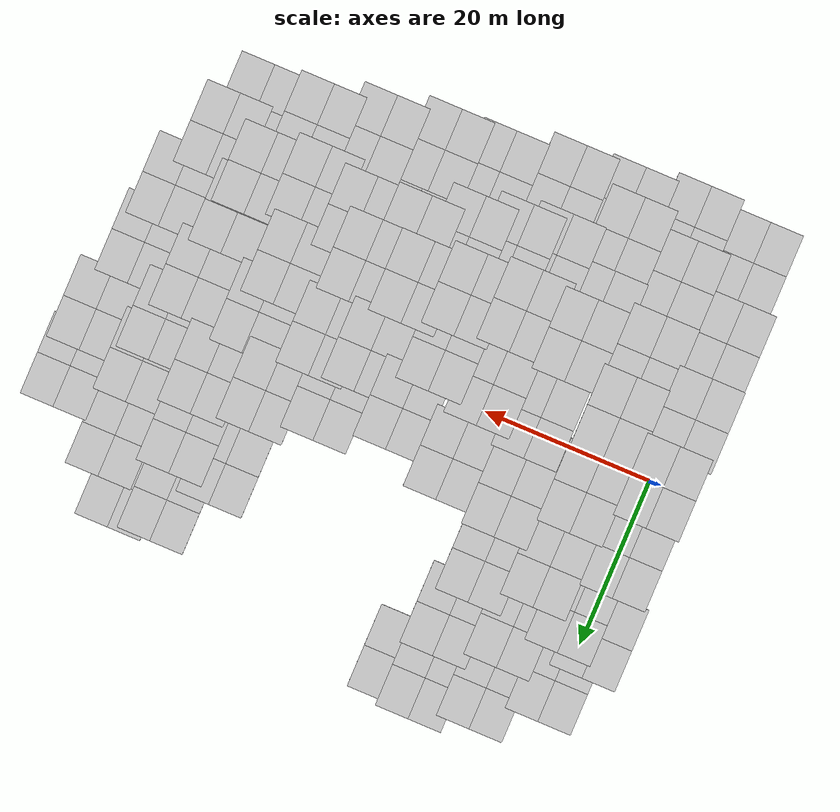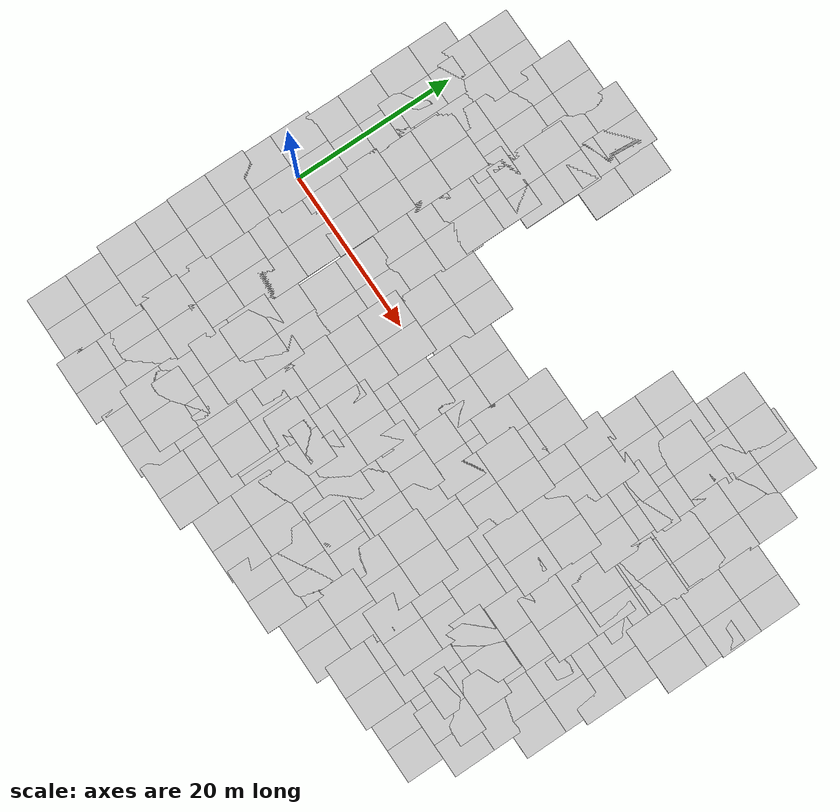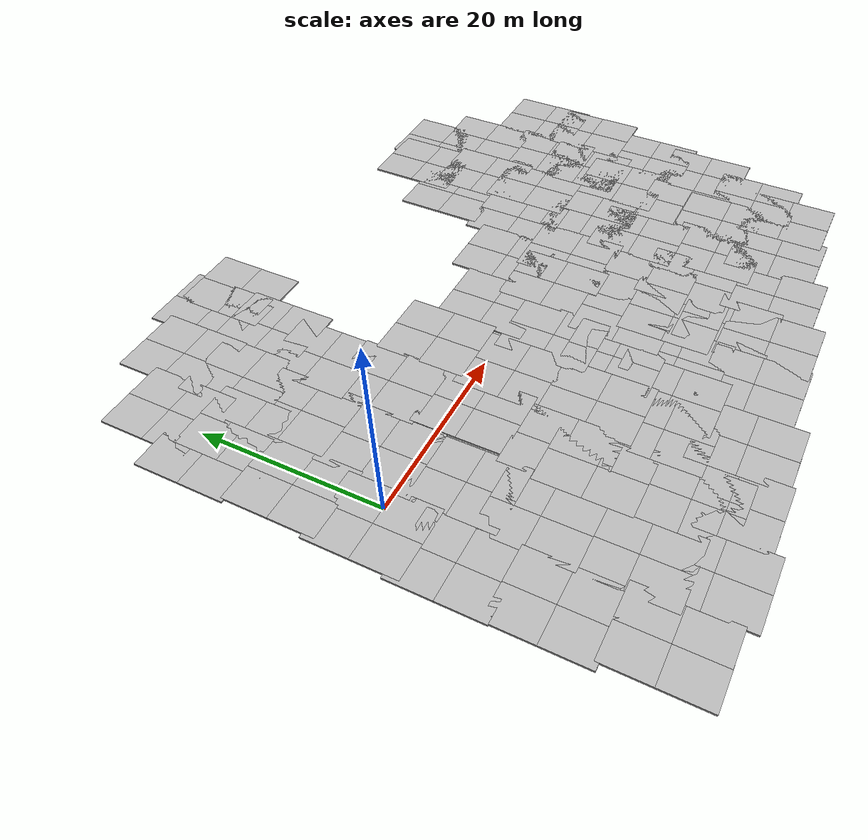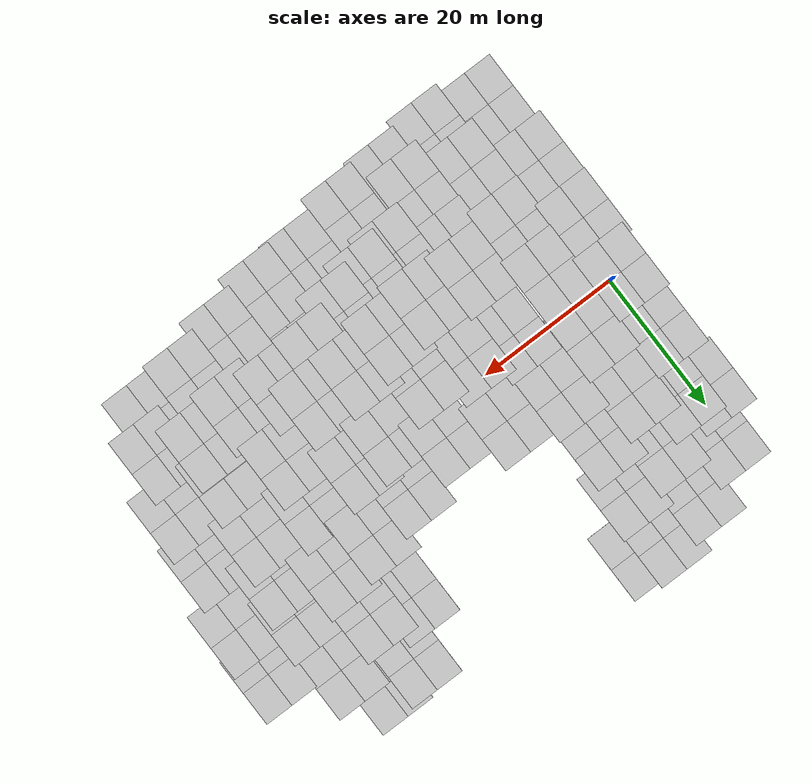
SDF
<sdf version="1.7">
 <world name="default">
  <plugin name="ros_interface_plugin" filename="librotors_gazebo_ros_interface_plugin.so"/>
  <light name="sun" type="directional">
   <pose>0 0 10 0 -0 0</pose>
   <diffuse>0.8 0.8 0.8 1</diffuse>
   <specular>0.2 0.2 0.2 1</specular>
   <attenuation>
    <range>1000</range>
    <constant>0.9</constant>
    <linear>0.01</linear>
    <quadratic>0.001</quadratic>
   </attenuation>
   <direction>-0.5 0.1 -0.9</direction>
   <spot><inner_angle>0</inner_angle><outer_angle>0</outer_angle><falloff>0</falloff></spot>
  </light>
  <gravity>0 0 -9.8</gravity>
  <magnetic_field>6e-06 2.3e-05 -4.2e-05</magnetic_field>
  <atmosphere type="adiabatic"/>
  <physics type="ode">
   <max_step_size>0.001</max_step_size>
   <real_time_factor>1</real_time_factor>
   <real_time_update_rate>1000</real_time_update_rate>
  </physics>
  <scene><ambient>0.4 0.4 0.4 1</ambient><background>0.7 0.7 0.7 1</background><shadows>1</shadows></scene>
  <spherical_coordinates>
   <surface_model>EARTH_WGS84</surface_model>
   <latitude_deg>0</latitude_deg>
   <longitude_deg>0</longitude_deg>
   <elevation>0</elevation>
   <heading_deg>0</heading_deg>
  </spherical_coordinates>
  <model name="mud_box">
   <static>1</static>
   <link name="link">
    <collision name="collision"><geometry><box><size>8 10 0.2</size></box></geometry></collision>
    <visual name="visual_1">
     <pose>-2 2.5 0 0 -0 0</pose>
     <cast_shadows>0</cast_shadows>
     <geometry><box><size>4 5 0.2</size></box></geometry>
     <material>
      <script>
       <uri>model://mud_box/materials/scripts</uri>
       <uri>model://mud_box/materials/textures</uri>
       <name>vrc/mud</name>
      </script>
     </material>
    </visual>
    <visual name="visual_2">
     <pose>2 2.5 0 0 -0 0</pose>
     <cast_shadows>0</cast_shadows>
     <geometry><box><size>4 5 0.2</size></box></geometry>
     <material>
      <script>
       <uri>model://mud_box/materials/scripts</uri>
       <uri>model://mud_box/materials/textures</uri>
       <name>vrc/mud</name>
      </script>
     </material>
    </visual>
    <visual name="visual_3">
     <pose>2 -2.5 0 0 -0 0</pose>
     <cast_shadows>0</cast_shadows>
     <geometry><box><size>4 5 0.2</size></box></geometry>
     <material>
      <script>
       <uri>model://mud_box/materials/scripts</uri>
       <uri>model://mud_box/materials/textures</uri>
       <name>vrc/mud</name>
      </script>
     </material>
    </visual>
    <visual name="visual_4">
     <pose>-2 -2.5 0 0 -0 0</pose>
     <cast_shadows>0</cast_shadows>
     <geometry><box><size>4 5 0.2</size></box></geometry>
     <material>
      <script>
       <uri>model://mud_box/materials/scripts</uri>
       <uri>model://mud_box/materials/textures</uri>
       <name>vrc/mud</name>
      </script>
     </material>
    </visual>
   </link>
   <pose>-1.75984 0.012929 0 0 -0 0</pose>
  </model>
  <model name="mud_box_clone">
   <static>1</static>
   <link name="link">
    <collision name="collision"><geometry><box><size>8 10 0.2</size></box></geometry></collision>
    <visual name="visual_1">
     <pose>-2 2.5 0 0 -0 0</pose>
     <cast_shadows>0</cast_shadows>
     <geometry><box><size>4 5 0.2</size></box></geometry>
     <material>
      <script>
       <uri>model://mud_box/materials/scripts</uri>
       <uri>model://mud_box/materials/textures</uri>
       <name>vrc/mud</name>
      </script>
     </material>
    </visual>
    <visual name="visual_2">
     <pose>2 2.5 0 0 -0 0</pose>
     <cast_shadows>0</cast_shadows>
     <geometry><box><size>4 5 0.2</size></box></geometry>
     <material>
      <script>
       <uri>model://mud_box/materials/scripts</uri>
       <uri>model://mud_box/materials/textures</uri>
       <name>vrc/mud</name>
      </script>
     </material>
    </visual>
    <visual name="visual_3">
     <pose>2 -2.5 0 0 -0 0</pose>
     <cast_shadows>0</cast_shadows>
     <geometry><box><size>4 5 0.2</size></box></geometry>
     <material>
      <script>
       <uri>model://mud_box/materials/scripts</uri>
       <uri>model://mud_box/materials/textures</uri>
       <name>vrc/mud</name>
      </script>
     </material>
    </visual>
    <visual name="visual_4">
     <pose>-2 -2.5 0 0 -0 0</pose>
     <cast_shadows>0</cast_shadows>
     <geometry><box><size>4 5 0.2</size></box></geometry>
     <material>
      <script>
       <uri>model://mud_box/materials/scripts</uri>
       <uri>model://mud_box/materials/textures</uri>
       <name>vrc/mud</name>
      </script>
     </material>
    </visual>
   </link>
   <pose>5.75179 -5.2884 0 0 -0 0</pose>
  </model>
  <model name="mud_box_clone_0">
   <static>1</static>
   <link name="link">
    <collision name="collision"><geometry><box><size>8 10 0.2</size></box></geometry></collision>
    <visual name="visual_1">
     <pose>-2 2.5 0 0 -0 0</pose>
     <cast_shadows>0</cast_shadows>
     <geometry><box><size>4 5 0.2</size></box></geometry>
     <material>
      <script>
       <uri>model://mud_box/materials/scripts</uri>
       <uri>model://mud_box/materials/textures</uri>
       <name>vrc/mud</name>
      </script>
     </material>
    </visual>
    <visual name="visual_2">
     <pose>2 2.5 0 0 -0 0</pose>
     <cast_shadows>0</cast_shadows>
     <geometry><box><size>4 5 0.2</size></box></geometry>
     <material>
      <script>
       <uri>model://mud_box/materials/scripts</uri>
       <uri>model://mud_box/materials/textures</uri>
       <name>vrc/mud</name>
      </script>
     </material>
    </visual>
    <visual name="visual_3">
     <pose>2 -2.5 0 0 -0 0</pose>
     <cast_shadows>0</cast_shadows>
     <geometry><box><size>4 5 0.2</size></box></geometry>
     <material>
      <script>
       <uri>model://mud_box/materials/scripts</uri>
       <uri>model://mud_box/materials/textures</uri>
       <name>vrc/mud</name>
      </script>
     </material>
    </visual>
    <visual name="visual_4">
     <pose>-2 -2.5 0 0 -0 0</pose>
     <cast_shadows>0</cast_shadows>
     <geometry><box><size>4 5 0.2</size></box></geometry>
     <material>
      <script>
       <uri>model://mud_box/materials/scripts</uri>
       <uri>model://mud_box/materials/textures</uri>
       <name>vrc/mud</name>
      </script>
     </material>
    </visual>
   </link>
   <pose>-2.14774 -8.41393 0 0 -0 0</pose>
  </model>
  <model name="mud_box_clone_1">
   <static>1</static>
   <link name="link">
    <collision name="collision"><geometry><box><size>8 10 0.2</size></box></geometry></collision>
    <visual name="visual_1">
     <pose>-2 2.5 0 0 -0 0</pose>
     <cast_shadows>0</cast_shadows>
     <geometry><box><size>4 5 0.2</size></box></geometry>
     <material>
      <script>
       <uri>model://mud_box/materials/scripts</uri>
       <uri>model://mud_box/materials/textures</uri>
       <name>vrc/mud</name>
      </script>
     </material>
    </visual>
    <visual name="visual_2">
     <pose>2 2.5 0 0 -0 0</pose>
     <cast_shadows>0</cast_shadows>
     <geometry><box><size>4 5 0.2</size></box></geometry>
     <material>
      <script>
       <uri>model://mud_box/materials/scripts</uri>
       <uri>model://mud_box/materials/textures</uri>
       <name>vrc/mud</name>
      </script>
     </material>
    </visual>
    <visual name="visual_3">
     <pose>2 -2.5 0 0 -0 0</pose>
     <cast_shadows>0</cast_shadows>
     <geometry><box><size>4 5 0.2</size></box></geometry>
     <material>
      <script>
       <uri>model://mud_box/materials/scripts</uri>
       <uri>model://mud_box/materials/textures</uri>
       <name>vrc/mud</name>
      </script>
     </material>
    </visual>
    <visual name="visual_4">
     <pose>-2 -2.5 0 0 -0 0</pose>
     <cast_shadows>0</cast_shadows>
     <geometry><box><size>4 5 0.2</size></box></geometry>
     <material>
      <script>
       <uri>model://mud_box/materials/scripts</uri>
       <uri>model://mud_box/materials/textures</uri>
       <name>vrc/mud</name>
      </script>
     </material>
    </visual>
   </link>
   <pose>5.95013 3.90898 0 0 -0 0</pose>
  </model>
  <model name="mud_box_clone_2">
   <static>1</static>
   <link name="link">
    <collision name="collision"><geometry><box><size>8 10 0.2</size></box></geometry></collision>
    <visual name="visual_1">
     <pose>-2 2.5 0 0 -0 0</pose>
     <cast_shadows>0</cast_shadows>
     <geometry><box><size>4 5 0.2</size></box></geometry>
     <material>
      <script>
       <uri>model://mud_box/materials/scripts</uri>
       <uri>model://mud_box/materials/textures</uri>
       <name>vrc/mud</name>
      </script>
     </material>
    </visual>
    <visual name="visual_2">
     <pose>2 2.5 0 0 -0 0</pose>
     <cast_shadows>0</cast_shadows>
     <geometry><box><size>4 5 0.2</size></box></geometry>
     <material>
      <script>
       <uri>model://mud_box/materials/scripts</uri>
       <uri>model://mud_box/materials/textures</uri>
       <name>vrc/mud</name>
      </script>
     </material>
    </visual>
    <visual name="visual_3">
     <pose>2 -2.5 0 0 -0 0</pose>
     <cast_shadows>0</cast_shadows>
     <geometry><box><size>4 5 0.2</size></box></geometry>
     <material>
      <script>
       <uri>model://mud_box/materials/scripts</uri>
       <uri>model://mud_box/materials/textures</uri>
       <name>vrc/mud</name>
      </script>
     </material>
    </visual>
    <visual name="visual_4">
     <pose>-2 -2.5 0 0 -0 0</pose>
     <cast_shadows>0</cast_shadows>
     <geometry><box><size>4 5 0.2</size></box></geometry>
     <material>
      <script>
       <uri>model://mud_box/materials/scripts</uri>
       <uri>model://mud_box/materials/textures</uri>
       <name>vrc/mud</name>
      </script>
     </material>
    </visual>
   </link>
   <pose>-1.33272 8.75434 0 0 -0 0</pose>
  </model>
  <model name="mud_box_clone_3">
   <static>1</static>
   <link name="link">
    <collision name="collision"><geometry><box><size>8 10 0.2</size></box></geometry></collision>
    <visual name="visual_1">
     <pose>-2 2.5 0 0 -0 0</pose>
     <cast_shadows>0</cast_shadows>
     <geometry><box><size>4 5 0.2</size></box></geometry>
     <material>
      <script>
       <uri>model://mud_box/materials/scripts</uri>
       <uri>model://mud_box/materials/textures</uri>
       <name>vrc/mud</name>
      </script>
     </material>
    </visual>
    <visual name="visual_2">
     <pose>2 2.5 0 0 -0 0</pose>
     <cast_shadows>0</cast_shadows>
     <geometry><box><size>4 5 0.2</size></box></geometry>
     <material>
      <script>
       <uri>model://mud_box/materials/scripts</uri>
       <uri>model://mud_box/materials/textures</uri>
       <name>vrc/mud</name>
      </script>
     </material>
    </visual>
    <visual name="visual_3">
     <pose>2 -2.5 0 0 -0 0</pose>
     <cast_shadows>0</cast_shadows>
     <geometry><box><size>4 5 0.2</size></box></geometry>
     <material>
      <script>
       <uri>model://mud_box/materials/scripts</uri>
       <uri>model://mud_box/materials/textures</uri>
       <name>vrc/mud</name>
      </script>
     </material>
    </visual>
    <visual name="visual_4">
     <pose>-2 -2.5 0 0 -0 0</pose>
     <cast_shadows>0</cast_shadows>
     <geometry><box><size>4 5 0.2</size></box></geometry>
     <material>
      <script>
       <uri>model://mud_box/materials/scripts</uri>
       <uri>model://mud_box/materials/textures</uri>
       <name>vrc/mud</name>
      </script>
     </material>
    </visual>
   </link>
   <pose>5.3204 -12.9035 0 0 -0 0</pose>
  </model>
  <model name="mud_box_clone_4">
   <static>1</static>
   <link name="link">
    <collision name="collision"><geometry><box><size>8 10 0.2</size></box></geometry></collision>
    <visual name="visual_1">
     <pose>-2 2.5 0 0 -0 0</pose>
     <cast_shadows>0</cast_shadows>
     <geometry><box><size>4 5 0.2</size></box></geometry>
     <material>
      <script>
       <uri>model://mud_box/materials/scripts</uri>
       <uri>model://mud_box/materials/textures</uri>
       <name>vrc/mud</name>
      </script>
     </material>
    </visual>
    <visual name="visual_2">
     <pose>2 2.5 0 0 -0 0</pose>
     <cast_shadows>0</cast_shadows>
     <geometry><box><size>4 5 0.2</size></box></geometry>
     <material>
      <script>
       <uri>model://mud_box/materials/scripts</uri>
       <uri>model://mud_box/materials/textures</uri>
       <name>vrc/mud</name>
      </script>
     </material>
    </visual>
    <visual name="visual_3">
     <pose>2 -2.5 0 0 -0 0</pose>
     <cast_shadows>0</cast_shadows>
     <geometry><box><size>4 5 0.2</size></box></geometry>
     <material>
      <script>
       <uri>model://mud_box/materials/scripts</uri>
       <uri>model://mud_box/materials/textures</uri>
       <name>vrc/mud</name>
      </script>
     </material>
    </visual>
    <visual name="visual_4">
     <pose>-2 -2.5 0 0 -0 0</pose>
     <cast_shadows>0</cast_shadows>
     <geometry><box><size>4 5 0.2</size></box></geometry>
     <material>
      <script>
       <uri>model://mud_box/materials/scripts</uri>
       <uri>model://mud_box/materials/textures</uri>
       <name>vrc/mud</name>
      </script>
     </material>
    </visual>
   </link>
   <pose>13.1524 -11.6244 0 0 -0 0</pose>
  </model>
  <model name="mud_box_clone_5">
   <static>1</static>
   <link name="link">
    <collision name="collision"><geometry><box><size>8 10 0.2</size></box></geometry></collision>
    <visual name="visual_1">
     <pose>-2 2.5 0 0 -0 0</pose>
     <cast_shadows>0</cast_shadows>
     <geometry><box><size>4 5 0.2</size></box></geometry>
     <material>
      <script>
       <uri>model://mud_box/materials/scripts</uri>
       <uri>model://mud_box/materials/textures</uri>
       <name>vrc/mud</name>
      </script>
     </material>
    </visual>
    <visual name="visual_2">
     <pose>2 2.5 0 0 -0 0</pose>
     <cast_shadows>0</cast_shadows>
     <geometry><box><size>4 5 0.2</size></box></geometry>
     <material>
      <script>
       <uri>model://mud_box/materials/scripts</uri>
       <uri>model://mud_box/materials/textures</uri>
       <name>vrc/mud</name>
      </script>
     </material>
    </visual>
    <visual name="visual_3">
     <pose>2 -2.5 0 0 -0 0</pose>
     <cast_shadows>0</cast_shadows>
     <geometry><box><size>4 5 0.2</size></box></geometry>
     <material>
      <script>
       <uri>model://mud_box/materials/scripts</uri>
       <uri>model://mud_box/materials/textures</uri>
       <name>vrc/mud</name>
      </script>
     </material>
    </visual>
    <visual name="visual_4">
     <pose>-2 -2.5 0 0 -0 0</pose>
     <cast_shadows>0</cast_shadows>
     <geometry><box><size>4 5 0.2</size></box></geometry>
     <material>
      <script>
       <uri>model://mud_box/materials/scripts</uri>
       <uri>model://mud_box/materials/textures</uri>
       <name>vrc/mud</name>
      </script>
     </material>
    </visual>
   </link>
   <pose>20.1809 -12.2756 0 0 -0 0</pose>
  </model>
  <model name="mud_box_clone_6">
   <static>1</static>
   <link name="link">
    <collision name="collision"><geometry><box><size>8 10 0.2</size></box></geometry></collision>
    <visual name="visual_1">
     <pose>-2 2.5 0 0 -0 0</pose>
     <cast_shadows>0</cast_shadows>
     <geometry><box><size>4 5 0.2</size></box></geometry>
     <material>
      <script>
       <uri>model://mud_box/materials/scripts</uri>
       <uri>model://mud_box/materials/textures</uri>
       <name>vrc/mud</name>
      </script>
     </material>
    </visual>
    <visual name="visual_2">
     <pose>2 2.5 0 0 -0 0</pose>
     <cast_shadows>0</cast_shadows>
     <geometry><box><size>4 5 0.2</size></box></geometry>
     <material>
      <script>
       <uri>model://mud_box/materials/scripts</uri>
       <uri>model://mud_box/materials/textures</uri>
       <name>vrc/mud</name>
      </script>
     </material>
    </visual>
    <visual name="visual_3">
     <pose>2 -2.5 0 0 -0 0</pose>
     <cast_shadows>0</cast_shadows>
     <geometry><box><size>4 5 0.2</size></box></geometry>
     <material>
      <script>
       <uri>model://mud_box/materials/scripts</uri>
       <uri>model://mud_box/materials/textures</uri>
       <name>vrc/mud</name>
      </script>
     </material>
    </visual>
    <visual name="visual_4">
     <pose>-2 -2.5 0 0 -0 0</pose>
     <cast_shadows>0</cast_shadows>
     <geometry><box><size>4 5 0.2</size></box></geometry>
     <material>
      <script>
       <uri>model://mud_box/materials/scripts</uri>
       <uri>model://mud_box/materials/textures</uri>
       <name>vrc/mud</name>
      </script>
     </material>
    </visual>
   </link>
   <pose>26.6295 -11.4951 0 0 -0 0</pose>
  </model>
  <model name="mud_box_clone_7">
   <static>1</static>
   <link name="link">
    <collision name="collision"><geometry><box><size>8 10 0.2</size></box></geometry></collision>
    <visual name="visual_1">
     <pose>-2 2.5 0 0 -0 0</pose>
     <cast_shadows>0</cast_shadows>
     <geometry><box><size>4 5 0.2</size></box></geometry>
     <material>
      <script>
       <uri>model://mud_box/materials/scripts</uri>
       <uri>model://mud_box/materials/textures</uri>
       <name>vrc/mud</name>
      </script>
     </material>
    </visual>
    <visual name="visual_2">
     <pose>2 2.5 0 0 -0 0</pose>
     <cast_shadows>0</cast_shadows>
     <geometry><box><size>4 5 0.2</size></box></geometry>
     <material>
      <script>
       <uri>model://mud_box/materials/scripts</uri>
       <uri>model://mud_box/materials/textures</uri>
       <name>vrc/mud</name>
      </script>
     </material>
    </visual>
    <visual name="visual_3">
     <pose>2 -2.5 0 0 -0 0</pose>
     <cast_shadows>0</cast_shadows>
     <geometry><box><size>4 5 0.2</size></box></geometry>
     <material>
      <script>
       <uri>model://mud_box/materials/scripts</uri>
       <uri>model://mud_box/materials/textures</uri>
       <name>vrc/mud</name>
      </script>
     </material>
    </visual>
    <visual name="visual_4">
     <pose>-2 -2.5 0 0 -0 0</pose>
     <cast_shadows>0</cast_shadows>
     <geometry><box><size>4 5 0.2</size></box></geometry>
     <material>
      <script>
       <uri>model://mud_box/materials/scripts</uri>
       <uri>model://mud_box/materials/textures</uri>
       <name>vrc/mud</name>
      </script>
     </material>
    </visual>
   </link>
   <pose>32.6832 -10.4811 0 0 -0 0</pose>
  </model>
  <model name="mud_box_clone_8">
   <static>1</static>
   <link name="link">
    <collision name="collision"><geometry><box><size>8 10 0.2</size></box></geometry></collision>
    <visual name="visual_1">
     <pose>-2 2.5 0 0 -0 0</pose>
     <cast_shadows>0</cast_shadows>
     <geometry><box><size>4 5 0.2</size></box></geometry>
     <material>
      <script>
       <uri>model://mud_box/materials/scripts</uri>
       <uri>model://mud_box/materials/textures</uri>
       <name>vrc/mud</name>
      </script>
     </material>
    </visual>
    <visual name="visual_2">
     <pose>2 2.5 0 0 -0 0</pose>
     <cast_shadows>0</cast_shadows>
     <geometry><box><size>4 5 0.2</size></box></geometry>
     <material>
      <script>
       <uri>model://mud_box/materials/scripts</uri>
       <uri>model://mud_box/materials/textures</uri>
       <name>vrc/mud</name>
      </script>
     </material>
    </visual>
    <visual name="visual_3">
     <pose>2 -2.5 0 0 -0 0</pose>
     <cast_shadows>0</cast_shadows>
     <geometry><box><size>4 5 0.2</size></box></geometry>
     <material>
      <script>
       <uri>model://mud_box/materials/scripts</uri>
       <uri>model://mud_box/materials/textures</uri>
       <name>vrc/mud</name>
      </script>
     </material>
    </visual>
    <visual name="visual_4">
     <pose>-2 -2.5 0 0 -0 0</pose>
     <cast_shadows>0</cast_shadows>
     <geometry><box><size>4 5 0.2</size></box></geometry>
     <material>
      <script>
       <uri>model://mud_box/materials/scripts</uri>
       <uri>model://mud_box/materials/textures</uri>
       <name>vrc/mud</name>
      </script>
     </material>
    </visual>
   </link>
   <pose>26.8669 -4.65584 0 0 -0 0</pose>
  </model>
  <model name="mud_box_clone_9">
   <static>1</static>
   <link name="link">
    <collision name="collision"><geometry><box><size>8 10 0.2</size></box></geometry></collision>
    <visual name="visual_1">
     <pose>-2 2.5 0 0 -0 0</pose>
     <cast_shadows>0</cast_shadows>
     <geometry><box><size>4 5 0.2</size></box></geometry>
     <material>
      <script>
       <uri>model://mud_box/materials/scripts</uri>
       <uri>model://mud_box/materials/textures</uri>
       <name>vrc/mud</name>
      </script>
     </material>
    </visual>
    <visual name="visual_2">
     <pose>2 2.5 0 0 -0 0</pose>
     <cast_shadows>0</cast_shadows>
     <geometry><box><size>4 5 0.2</size></box></geometry>
     <material>
      <script>
       <uri>model://mud_box/materials/scripts</uri>
       <uri>model://mud_box/materials/textures</uri>
       <name>vrc/mud</name>
      </script>
     </material>
    </visual>
    <visual name="visual_3">
     <pose>2 -2.5 0 0 -0 0</pose>
     <cast_shadows>0</cast_shadows>
     <geometry><box><size>4 5 0.2</size></box></geometry>
     <material>
      <script>
       <uri>model://mud_box/materials/scripts</uri>
       <uri>model://mud_box/materials/textures</uri>
       <name>vrc/mud</name>
      </script>
     </material>
    </visual>
    <visual name="visual_4">
     <pose>-2 -2.5 0 0 -0 0</pose>
     <cast_shadows>0</cast_shadows>
     <geometry><box><size>4 5 0.2</size></box></geometry>
     <material>
      <script>
       <uri>model://mud_box/materials/scripts</uri>
       <uri>model://mud_box/materials/textures</uri>
       <name>vrc/mud</name>
      </script>
     </material>
    </visual>
   </link>
   <pose>20.3748 -3.19662 0 0 -0 0</pose>
  </model>
  <model name="mud_box_clone_10">
   <static>1</static>
   <link name="link">
    <collision name="collision"><geometry><box><size>8 10 0.2</size></box></geometry></collision>
    <visual name="visual_1">
     <pose>-2 2.5 0 0 -0 0</pose>
     <cast_shadows>0</cast_shadows>
     <geometry><box><size>4 5 0.2</size></box></geometry>
     <material>
      <script>
       <uri>model://mud_box/materials/scripts</uri>
       <uri>model://mud_box/materials/textures</uri>
       <name>vrc/mud</name>
      </script>
     </material>
    </visual>
    <visual name="visual_2">
     <pose>2 2.5 0 0 -0 0</pose>
     <cast_shadows>0</cast_shadows>
     <geometry><box><size>4 5 0.2</size></box></geometry>
     <material>
      <script>
       <uri>model://mud_box/materials/scripts</uri>
       <uri>model://mud_box/materials/textures</uri>
       <name>vrc/mud</name>
      </script>
     </material>
    </visual>
    <visual name="visual_3">
     <pose>2 -2.5 0 0 -0 0</pose>
     <cast_shadows>0</cast_shadows>
     <geometry><box><size>4 5 0.2</size></box></geometry>
     <material>
      <script>
       <uri>model://mud_box/materials/scripts</uri>
       <uri>model://mud_box/materials/textures</uri>
       <name>vrc/mud</name>
      </script>
     </material>
    </visual>
    <visual name="visual_4">
     <pose>-2 -2.5 0 0 -0 0</pose>
     <cast_shadows>0</cast_shadows>
     <geometry><box><size>4 5 0.2</size></box></geometry>
     <material>
      <script>
       <uri>model://mud_box/materials/scripts</uri>
       <uri>model://mud_box/materials/textures</uri>
       <name>vrc/mud</name>
      </script>
     </material>
    </visual>
   </link>
   <pose>14.0105 -1.86425 0 0 -0 0</pose>
  </model>
  <model name="mud_box_clone_11">
   <static>1</static>
   <link name="link">
    <collision name="collision"><geometry><box><size>8 10 0.2</size></box></geometry></collision>
    <visual name="visual_1">
     <pose>-2 2.5 0 0 -0 0</pose>
     <cast_shadows>0</cast_shadows>
     <geometry><box><size>4 5 0.2</size></box></geometry>
     <material>
      <script>
       <uri>model://mud_box/materials/scripts</uri>
       <uri>model://mud_box/materials/textures</uri>
       <name>vrc/mud</name>
      </script>
     </material>
    </visual>
    <visual name="visual_2">
     <pose>2 2.5 0 0 -0 0</pose>
     <cast_shadows>0</cast_shadows>
     <geometry><box><size>4 5 0.2</size></box></geometry>
     <material>
      <script>
       <uri>model://mud_box/materials/scripts</uri>
       <uri>model://mud_box/materials/textures</uri>
       <name>vrc/mud</name>
      </script>
     </material>
    </visual>
    <visual name="visual_3">
     <pose>2 -2.5 0 0 -0 0</pose>
     <cast_shadows>0</cast_shadows>
     <geometry><box><size>4 5 0.2</size></box></geometry>
     <material>
      <script>
       <uri>model://mud_box/materials/scripts</uri>
       <uri>model://mud_box/materials/textures</uri>
       <name>vrc/mud</name>
      </script>
     </material>
    </visual>
    <visual name="visual_4">
     <pose>-2 -2.5 0 0 -0 0</pose>
     <cast_shadows>0</cast_shadows>
     <geometry><box><size>4 5 0.2</size></box></geometry>
     <material>
      <script>
       <uri>model://mud_box/materials/scripts</uri>
       <uri>model://mud_box/materials/textures</uri>
       <name>vrc/mud</name>
      </script>
     </material>
    </visual>
   </link>
   <pose>13.6359 7.58583 0 0 -0 0</pose>
  </model>
  <model name="mud_box_clone_12">
   <static>1</static>
   <link name="link">
    <collision name="collision"><geometry><box><size>8 10 0.2</size></box></geometry></collision>
    <visual name="visual_1">
     <pose>-2 2.5 0 0 -0 0</pose>
     <cast_shadows>0</cast_shadows>
     <geometry><box><size>4 5 0.2</size></box></geometry>
     <material>
      <script>
       <uri>model://mud_box/materials/scripts</uri>
       <uri>model://mud_box/materials/textures</uri>
       <name>vrc/mud</name>
      </script>
     </material>
    </visual>
    <visual name="visual_2">
     <pose>2 2.5 0 0 -0 0</pose>
     <cast_shadows>0</cast_shadows>
     <geometry><box><size>4 5 0.2</size></box></geometry>
     <material>
      <script>
       <uri>model://mud_box/materials/scripts</uri>
       <uri>model://mud_box/materials/textures</uri>
       <name>vrc/mud</name>
      </script>
     </material>
    </visual>
    <visual name="visual_3">
     <pose>2 -2.5 0 0 -0 0</pose>
     <cast_shadows>0</cast_shadows>
     <geometry><box><size>4 5 0.2</size></box></geometry>
     <material>
      <script>
       <uri>model://mud_box/materials/scripts</uri>
       <uri>model://mud_box/materials/textures</uri>
       <name>vrc/mud</name>
      </script>
     </material>
    </visual>
    <visual name="visual_4">
     <pose>-2 -2.5 0 0 -0 0</pose>
     <cast_shadows>0</cast_shadows>
     <geometry><box><size>4 5 0.2</size></box></geometry>
     <material>
      <script>
       <uri>model://mud_box/materials/scripts</uri>
       <uri>model://mud_box/materials/textures</uri>
       <name>vrc/mud</name>
      </script>
     </material>
    </visual>
   </link>
   <pose>6.50548 13.1761 0 0 -0 0</pose>
  </model>
  <model name="mud_box_clone_13">
   <static>1</static>
   <link name="link">
    <collision name="collision"><geometry><box><size>8 10 0.2</size></box></geometry></collision>
    <visual name="visual_1">
     <pose>-2 2.5 0 0 -0 0</pose>
     <cast_shadows>0</cast_shadows>
     <geometry><box><size>4 5 0.2</size></box></geometry>
     <material>
      <script>
       <uri>model://mud_box/materials/scripts</uri>
       <uri>model://mud_box/materials/textures</uri>
       <name>vrc/mud</name>
      </script>
     </material>
    </visual>
    <visual name="visual_2">
     <pose>2 2.5 0 0 -0 0</pose>
     <cast_shadows>0</cast_shadows>
     <geometry><box><size>4 5 0.2</size></box></geometry>
     <material>
      <script>
       <uri>model://mud_box/materials/scripts</uri>
       <uri>model://mud_box/materials/textures</uri>
       <name>vrc/mud</name>
      </script>
     </material>
    </visual>
    <visual name="visual_3">
     <pose>2 -2.5 0 0 -0 0</pose>
     <cast_shadows>0</cast_shadows>
     <geometry><box><size>4 5 0.2</size></box></geometry>
     <material>
      <script>
       <uri>model://mud_box/materials/scripts</uri>
       <uri>model://mud_box/materials/textures</uri>
       <name>vrc/mud</name>
      </script>
     </material>
    </visual>
    <visual name="visual_4">
     <pose>-2 -2.5 0 0 -0 0</pose>
     <cast_shadows>0</cast_shadows>
     <geometry><box><size>4 5 0.2</size></box></geometry>
     <material>
      <script>
       <uri>model://mud_box/materials/scripts</uri>
       <uri>model://mud_box/materials/textures</uri>
       <name>vrc/mud</name>
      </script>
     </material>
    </visual>
   </link>
   <pose>21.3167 6.26549 0 0 -0 0</pose>
  </model>
  <model name="mud_box_clone_14">
   <static>1</static>
   <link name="link">
    <collision name="collision"><geometry><box><size>8 10 0.2</size></box></geometry></collision>
    <visual name="visual_1">
     <pose>-2 2.5 0 0 -0 0</pose>
     <cast_shadows>0</cast_shadows>
     <geometry><box><size>4 5 0.2</size></box></geometry>
     <material>
      <script>
       <uri>model://mud_box/materials/scripts</uri>
       <uri>model://mud_box/materials/textures</uri>
       <name>vrc/mud</name>
      </script>
     </material>
    </visual>
    <visual name="visual_2">
     <pose>2 2.5 0 0 -0 0</pose>
     <cast_shadows>0</cast_shadows>
     <geometry><box><size>4 5 0.2</size></box></geometry>
     <material>
      <script>
       <uri>model://mud_box/materials/scripts</uri>
       <uri>model://mud_box/materials/textures</uri>
       <name>vrc/mud</name>
      </script>
     </material>
    </visual>
    <visual name="visual_3">
     <pose>2 -2.5 0 0 -0 0</pose>
     <cast_shadows>0</cast_shadows>
     <geometry><box><size>4 5 0.2</size></box></geometry>
     <material>
      <script>
       <uri>model://mud_box/materials/scripts</uri>
       <uri>model://mud_box/materials/textures</uri>
       <name>vrc/mud</name>
      </script>
     </material>
    </visual>
    <visual name="visual_4">
     <pose>-2 -2.5 0 0 -0 0</pose>
     <cast_shadows>0</cast_shadows>
     <geometry><box><size>4 5 0.2</size></box></geometry>
     <material>
      <script>
       <uri>model://mud_box/materials/scripts</uri>
       <uri>model://mud_box/materials/textures</uri>
       <name>vrc/mud</name>
      </script>
     </material>
    </visual>
   </link>
   <pose>28.7382 3.2623 0 0 -0 0</pose>
  </model>
  <model name="mud_box_clone_15">
   <static>1</static>
   <link name="link">
    <collision name="collision"><geometry><box><size>8 10 0.2</size></box></geometry></collision>
    <visual name="visual_1">
     <pose>-2 2.5 0 0 -0 0</pose>
     <cast_shadows>0</cast_shadows>
     <geometry><box><size>4 5 0.2</size></box></geometry>
     <material>
      <script>
       <uri>model://mud_box/materials/scripts</uri>
       <uri>model://mud_box/materials/textures</uri>
       <name>vrc/mud</name>
      </script>
     </material>
    </visual>
    <visual name="visual_2">
     <pose>2 2.5 0 0 -0 0</pose>
     <cast_shadows>0</cast_shadows>
     <geometry><box><size>4 5 0.2</size></box></geometry>
     <material>
      <script>
       <uri>model://mud_box/materials/scripts</uri>
       <uri>model://mud_box/materials/textures</uri>
       <name>vrc/mud</name>
      </script>
     </material>
    </visual>
    <visual name="visual_3">
     <pose>2 -2.5 0 0 -0 0</pose>
     <cast_shadows>0</cast_shadows>
     <geometry><box><size>4 5 0.2</size></box></geometry>
     <material>
      <script>
       <uri>model://mud_box/materials/scripts</uri>
       <uri>model://mud_box/materials/textures</uri>
       <name>vrc/mud</name>
      </script>
     </material>
    </visual>
    <visual name="visual_4">
     <pose>-2 -2.5 0 0 -0 0</pose>
     <cast_shadows>0</cast_shadows>
     <geometry><box><size>4 5 0.2</size></box></geometry>
     <material>
      <script>
       <uri>model://mud_box/materials/scripts</uri>
       <uri>model://mud_box/materials/textures</uri>
       <name>vrc/mud</name>
      </script>
     </material>
    </visual>
   </link>
   <pose>34.5719 -1.36093 0 0 -0 0</pose>
  </model>
  <model name="mud_box_clone_16">
   <static>1</static>
   <link name="link">
    <collision name="collision"><geometry><box><size>8 10 0.2</size></box></geometry></collision>
    <visual name="visual_1">
     <pose>-2 2.5 0 0 -0 0</pose>
     <cast_shadows>0</cast_shadows>
     <geometry><box><size>4 5 0.2</size></box></geometry>
     <material>
      <script>
       <uri>model://mud_box/materials/scripts</uri>
       <uri>model://mud_box/materials/textures</uri>
       <name>vrc/mud</name>
      </script>
     </material>
    </visual>
    <visual name="visual_2">
     <pose>2 2.5 0 0 -0 0</pose>
     <cast_shadows>0</cast_shadows>
     <geometry><box><size>4 5 0.2</size></box></geometry>
     <material>
      <script>
       <uri>model://mud_box/materials/scripts</uri>
       <uri>model://mud_box/materials/textures</uri>
       <name>vrc/mud</name>
      </script>
     </material>
    </visual>
    <visual name="visual_3">
     <pose>2 -2.5 0 0 -0 0</pose>
     <cast_shadows>0</cast_shadows>
     <geometry><box><size>4 5 0.2</size></box></geometry>
     <material>
      <script>
       <uri>model://mud_box/materials/scripts</uri>
       <uri>model://mud_box/materials/textures</uri>
       <name>vrc/mud</name>
      </script>
     </material>
    </visual>
    <visual name="visual_4">
     <pose>-2 -2.5 0 0 -0 0</pose>
     <cast_shadows>0</cast_shadows>
     <geometry><box><size>4 5 0.2</size></box></geometry>
     <material>
      <script>
       <uri>model://mud_box/materials/scripts</uri>
       <uri>model://mud_box/materials/textures</uri>
       <name>vrc/mud</name>
      </script>
     </material>
    </visual>
   </link>
   <pose>39.0529 -10.4513 0 0 -0 0</pose>
  </model>
  <model name="mud_box_clone_17">
   <static>1</static>
   <link name="link">
    <collision name="collision"><geometry><box><size>8 10 0.2</size></box></geometry></collision>
    <visual name="visual_1">
     <pose>-2 2.5 0 0 -0 0</pose>
     <cast_shadows>0</cast_shadows>
     <geometry><box><size>4 5 0.2</size></box></geometry>
     <material>
      <script>
       <uri>model://mud_box/materials/scripts</uri>
       <uri>model://mud_box/materials/textures</uri>
       <name>vrc/mud</name>
      </script>
     </material>
    </visual>
    <visual name="visual_2">
     <pose>2 2.5 0 0 -0 0</pose>
     <cast_shadows>0</cast_shadows>
     <geometry><box><size>4 5 0.2</size></box></geometry>
     <material>
      <script>
       <uri>model://mud_box/materials/scripts</uri>
       <uri>model://mud_box/materials/textures</uri>
       <name>vrc/mud</name>
      </script>
     </material>
    </visual>
    <visual name="visual_3">
     <pose>2 -2.5 0 0 -0 0</pose>
     <cast_shadows>0</cast_shadows>
     <geometry><box><size>4 5 0.2</size></box></geometry>
     <material>
      <script>
       <uri>model://mud_box/materials/scripts</uri>
       <uri>model://mud_box/materials/textures</uri>
       <name>vrc/mud</name>
      </script>
     </material>
    </visual>
    <visual name="visual_4">
     <pose>-2 -2.5 0 0 -0 0</pose>
     <cast_shadows>0</cast_shadows>
     <geometry><box><size>4 5 0.2</size></box></geometry>
     <material>
      <script>
       <uri>model://mud_box/materials/scripts</uri>
       <uri>model://mud_box/materials/textures</uri>
       <name>vrc/mud</name>
      </script>
     </material>
    </visual>
   </link>
   <pose>34.9828 -15.1139 0 0 -0 0</pose>
  </model>
  <model name="mud_box_clone_18">
   <static>1</static>
   <link name="link">
    <collision name="collision"><geometry><box><size>8 10 0.2</size></box></geometry></collision>
    <visual name="visual_1">
     <pose>-2 2.5 0 0 -0 0</pose>
     <cast_shadows>0</cast_shadows>
     <geometry><box><size>4 5 0.2</size></box></geometry>
     <material>
      <script>
       <uri>model://mud_box/materials/scripts</uri>
       <uri>model://mud_box/materials/textures</uri>
       <name>vrc/mud</name>
      </script>
     </material>
    </visual>
    <visual name="visual_2">
     <pose>2 2.5 0 0 -0 0</pose>
     <cast_shadows>0</cast_shadows>
     <geometry><box><size>4 5 0.2</size></box></geometry>
     <material>
      <script>
       <uri>model://mud_box/materials/scripts</uri>
       <uri>model://mud_box/materials/textures</uri>
       <name>vrc/mud</name>
      </script>
     </material>
    </visual>
    <visual name="visual_3">
     <pose>2 -2.5 0 0 -0 0</pose>
     <cast_shadows>0</cast_shadows>
     <geometry><box><size>4 5 0.2</size></box></geometry>
     <material>
      <script>
       <uri>model://mud_box/materials/scripts</uri>
       <uri>model://mud_box/materials/textures</uri>
       <name>vrc/mud</name>
      </script>
     </material>
    </visual>
    <visual name="visual_4">
     <pose>-2 -2.5 0 0 -0 0</pose>
     <cast_shadows>0</cast_shadows>
     <geometry><box><size>4 5 0.2</size></box></geometry>
     <material>
      <script>
       <uri>model://mud_box/materials/scripts</uri>
       <uri>model://mud_box/materials/textures</uri>
       <name>vrc/mud</name>
      </script>
     </material>
    </visual>
   </link>
   <pose>29.3659 -17.4504 0 0 -0 0</pose>
  </model>
  <model name="mud_box_clone_19">
   <static>1</static>
   <link name="link">
    <collision name="collision"><geometry><box><size>8 10 0.2</size></box></geometry></collision>
    <visual name="visual_1">
     <pose>-2 2.5 0 0 -0 0</pose>
     <cast_shadows>0</cast_shadows>
     <geometry><box><size>4 5 0.2</size></box></geometry>
     <material>
      <script>
       <uri>model://mud_box/materials/scripts</uri>
       <uri>model://mud_box/materials/textures</uri>
       <name>vrc/mud</name>
      </script>
     </material>
    </visual>
    <visual name="visual_2">
     <pose>2 2.5 0 0 -0 0</pose>
     <cast_shadows>0</cast_shadows>
     <geometry><box><size>4 5 0.2</size></box></geometry>
     <material>
      <script>
       <uri>model://mud_box/materials/scripts</uri>
       <uri>model://mud_box/materials/textures</uri>
       <name>vrc/mud</name>
      </script>
     </material>
    </visual>
    <visual name="visual_3">
     <pose>2 -2.5 0 0 -0 0</pose>
     <cast_shadows>0</cast_shadows>
     <geometry><box><size>4 5 0.2</size></box></geometry>
     <material>
      <script>
       <uri>model://mud_box/materials/scripts</uri>
       <uri>model://mud_box/materials/textures</uri>
       <name>vrc/mud</name>
      </script>
     </material>
    </visual>
    <visual name="visual_4">
     <pose>-2 -2.5 0 0 -0 0</pose>
     <cast_shadows>0</cast_shadows>
     <geometry><box><size>4 5 0.2</size></box></geometry>
     <material>
      <script>
       <uri>model://mud_box/materials/scripts</uri>
       <uri>model://mud_box/materials/textures</uri>
       <name>vrc/mud</name>
      </script>
     </material>
    </visual>
   </link>
   <pose>24.0056 -18.6663 0 0 -0 0</pose>
  </model>
  <model name="mud_box_clone_20">
   <static>1</static>
   <link name="link">
    <collision name="collision"><geometry><box><size>8 10 0.2</size></box></geometry></collision>
    <visual name="visual_1">
     <pose>-2 2.5 0 0 -0 0</pose>
     <cast_shadows>0</cast_shadows>
     <geometry><box><size>4 5 0.2</size></box></geometry>
     <material>
      <script>
       <uri>model://mud_box/materials/scripts</uri>
       <uri>model://mud_box/materials/textures</uri>
       <name>vrc/mud</name>
      </script>
     </material>
    </visual>
    <visual name="visual_2">
     <pose>2 2.5 0 0 -0 0</pose>
     <cast_shadows>0</cast_shadows>
     <geometry><box><size>4 5 0.2</size></box></geometry>
     <material>
      <script>
       <uri>model://mud_box/materials/scripts</uri>
       <uri>model://mud_box/materials/textures</uri>
       <name>vrc/mud</name>
      </script>
     </material>
    </visual>
    <visual name="visual_3">
     <pose>2 -2.5 0 0 -0 0</pose>
     <cast_shadows>0</cast_shadows>
     <geometry><box><size>4 5 0.2</size></box></geometry>
     <material>
      <script>
       <uri>model://mud_box/materials/scripts</uri>
       <uri>model://mud_box/materials/textures</uri>
       <name>vrc/mud</name>
      </script>
     </material>
    </visual>
    <visual name="visual_4">
     <pose>-2 -2.5 0 0 -0 0</pose>
     <cast_shadows>0</cast_shadows>
     <geometry><box><size>4 5 0.2</size></box></geometry>
     <material>
      <script>
       <uri>model://mud_box/materials/scripts</uri>
       <uri>model://mud_box/materials/textures</uri>
       <name>vrc/mud</name>
      </script>
     </material>
    </visual>
   </link>
   <pose>19.5061 -19.4059 0 0 -0 0</pose>
  </model>
  <model name="mud_box_clone_21">
   <static>1</static>
   <link name="link">
    <collision name="collision"><geometry><box><size>8 10 0.2</size></box></geometry></collision>
    <visual name="visual_1">
     <pose>-2 2.5 0 0 -0 0</pose>
     <cast_shadows>0</cast_shadows>
     <geometry><box><size>4 5 0.2</size></box></geometry>
     <material>
      <script>
       <uri>model://mud_box/materials/scripts</uri>
       <uri>model://mud_box/materials/textures</uri>
       <name>vrc/mud</name>
      </script>
     </material>
    </visual>
    <visual name="visual_2">
     <pose>2 2.5 0 0 -0 0</pose>
     <cast_shadows>0</cast_shadows>
     <geometry><box><size>4 5 0.2</size></box></geometry>
     <material>
      <script>
       <uri>model://mud_box/materials/scripts</uri>
       <uri>model://mud_box/materials/textures</uri>
       <name>vrc/mud</name>
      </script>
     </material>
    </visual>
    <visual name="visual_3">
     <pose>2 -2.5 0 0 -0 0</pose>
     <cast_shadows>0</cast_shadows>
     <geometry><box><size>4 5 0.2</size></box></geometry>
     <material>
      <script>
       <uri>model://mud_box/materials/scripts</uri>
       <uri>model://mud_box/materials/textures</uri>
       <name>vrc/mud</name>
      </script>
     </material>
    </visual>
    <visual name="visual_4">
     <pose>-2 -2.5 0 0 -0 0</pose>
     <cast_shadows>0</cast_shadows>
     <geometry><box><size>4 5 0.2</size></box></geometry>
     <material>
      <script>
       <uri>model://mud_box/materials/scripts</uri>
       <uri>model://mud_box/materials/textures</uri>
       <name>vrc/mud</name>
      </script>
     </material>
    </visual>
   </link>
   <pose>41.4562 -14.7087 0 0 -0 0</pose>
  </model>
  <model name="mud_box_clone_22">
   <static>1</static>
   <link name="link">
    <collision name="collision"><geometry><box><size>8 10 0.2</size></box></geometry></collision>
    <visual name="visual_1">
     <pose>-2 2.5 0 0 -0 0</pose>
     <cast_shadows>0</cast_shadows>
     <geometry><box><size>4 5 0.2</size></box></geometry>
     <material>
      <script>
       <uri>model://mud_box/materials/scripts</uri>
       <uri>model://mud_box/materials/textures</uri>
       <name>vrc/mud</name>
      </script>
     </material>
    </visual>
    <visual name="visual_2">
     <pose>2 2.5 0 0 -0 0</pose>
     <cast_shadows>0</cast_shadows>
     <geometry><box><size>4 5 0.2</size></box></geometry>
     <material>
      <script>
       <uri>model://mud_box/materials/scripts</uri>
       <uri>model://mud_box/materials/textures</uri>
       <name>vrc/mud</name>
      </script>
     </material>
    </visual>
    <visual name="visual_3">
     <pose>2 -2.5 0 0 -0 0</pose>
     <cast_shadows>0</cast_shadows>
     <geometry><box><size>4 5 0.2</size></box></geometry>
     <material>
      <script>
       <uri>model://mud_box/materials/scripts</uri>
       <uri>model://mud_box/materials/textures</uri>
       <name>vrc/mud</name>
      </script>
     </material>
    </visual>
    <visual name="visual_4">
     <pose>-2 -2.5 0 0 -0 0</pose>
     <cast_shadows>0</cast_shadows>
     <geometry><box><size>4 5 0.2</size></box></geometry>
     <material>
      <script>
       <uri>model://mud_box/materials/scripts</uri>
       <uri>model://mud_box/materials/textures</uri>
       <name>vrc/mud</name>
      </script>
     </material>
    </visual>
   </link>
   <pose>39.9973 -0.999067 0 0 -0 0</pose>
  </model>
  <model name="mud_box_clone_23">
   <static>1</static>
   <link name="link">
    <collision name="collision"><geometry><box><size>8 10 0.2</size></box></geometry></collision>
    <visual name="visual_1">
     <pose>-2 2.5 0 0 -0 0</pose>
     <cast_shadows>0</cast_shadows>
     <geometry><box><size>4 5 0.2</size></box></geometry>
     <material>
      <script>
       <uri>model://mud_box/materials/scripts</uri>
       <uri>model://mud_box/materials/textures</uri>
       <name>vrc/mud</name>
      </script>
     </material>
    </visual>
    <visual name="visual_2">
     <pose>2 2.5 0 0 -0 0</pose>
     <cast_shadows>0</cast_shadows>
     <geometry><box><size>4 5 0.2</size></box></geometry>
     <material>
      <script>
       <uri>model://mud_box/materials/scripts</uri>
       <uri>model://mud_box/materials/textures</uri>
       <name>vrc/mud</name>
      </script>
     </material>
    </visual>
    <visual name="visual_3">
     <pose>2 -2.5 0 0 -0 0</pose>
     <cast_shadows>0</cast_shadows>
     <geometry><box><size>4 5 0.2</size></box></geometry>
     <material>
      <script>
       <uri>model://mud_box/materials/scripts</uri>
       <uri>model://mud_box/materials/textures</uri>
       <name>vrc/mud</name>
      </script>
     </material>
    </visual>
    <visual name="visual_4">
     <pose>-2 -2.5 0 0 -0 0</pose>
     <cast_shadows>0</cast_shadows>
     <geometry><box><size>4 5 0.2</size></box></geometry>
     <material>
      <script>
       <uri>model://mud_box/materials/scripts</uri>
       <uri>model://mud_box/materials/textures</uri>
       <name>vrc/mud</name>
      </script>
     </material>
    </visual>
   </link>
   <pose>36.6587 5.53181 0 0 -0 0</pose>
  </model>
  <model name="mud_box_clone_24">
   <static>1</static>
   <link name="link">
    <collision name="collision"><geometry><box><size>8 10 0.2</size></box></geometry></collision>
    <visual name="visual_1">
     <pose>-2 2.5 0 0 -0 0</pose>
     <cast_shadows>0</cast_shadows>
     <geometry><box><size>4 5 0.2</size></box></geometry>
     <material>
      <script>
       <uri>model://mud_box/materials/scripts</uri>
       <uri>model://mud_box/materials/textures</uri>
       <name>vrc/mud</name>
      </script>
     </material>
    </visual>
    <visual name="visual_2">
     <pose>2 2.5 0 0 -0 0</pose>
     <cast_shadows>0</cast_shadows>
     <geometry><box><size>4 5 0.2</size></box></geometry>
     <material>
      <script>
       <uri>model://mud_box/materials/scripts</uri>
       <uri>model://mud_box/materials/textures</uri>
       <name>vrc/mud</name>
      </script>
     </material>
    </visual>
    <visual name="visual_3">
     <pose>2 -2.5 0 0 -0 0</pose>
     <cast_shadows>0</cast_shadows>
     <geometry><box><size>4 5 0.2</size></box></geometry>
     <material>
      <script>
       <uri>model://mud_box/materials/scripts</uri>
       <uri>model://mud_box/materials/textures</uri>
       <name>vrc/mud</name>
      </script>
     </material>
    </visual>
    <visual name="visual_4">
     <pose>-2 -2.5 0 0 -0 0</pose>
     <cast_shadows>0</cast_shadows>
     <geometry><box><size>4 5 0.2</size></box></geometry>
     <material>
      <script>
       <uri>model://mud_box/materials/scripts</uri>
       <uri>model://mud_box/materials/textures</uri>
       <name>vrc/mud</name>
      </script>
     </material>
    </visual>
   </link>
   <pose>43.725 7.4379 0 0 -0 0</pose>
  </model>
  <model name="mud_box_clone_25">
   <static>1</static>
   <link name="link">
    <collision name="collision"><geometry><box><size>8 10 0.2</size></box></geometry></collision>
    <visual name="visual_1">
     <pose>-2 2.5 0 0 -0 0</pose>
     <cast_shadows>0</cast_shadows>
     <geometry><box><size>4 5 0.2</size></box></geometry>
     <material>
      <script>
       <uri>model://mud_box/materials/scripts</uri>
       <uri>model://mud_box/materials/textures</uri>
       <name>vrc/mud</name>
      </script>
     </material>
    </visual>
    <visual name="visual_2">
     <pose>2 2.5 0 0 -0 0</pose>
     <cast_shadows>0</cast_shadows>
     <geometry><box><size>4 5 0.2</size></box></geometry>
     <material>
      <script>
       <uri>model://mud_box/materials/scripts</uri>
       <uri>model://mud_box/materials/textures</uri>
       <name>vrc/mud</name>
      </script>
     </material>
    </visual>
    <visual name="visual_3">
     <pose>2 -2.5 0 0 -0 0</pose>
     <cast_shadows>0</cast_shadows>
     <geometry><box><size>4 5 0.2</size></box></geometry>
     <material>
      <script>
       <uri>model://mud_box/materials/scripts</uri>
       <uri>model://mud_box/materials/textures</uri>
       <name>vrc/mud</name>
      </script>
     </material>
    </visual>
    <visual name="visual_4">
     <pose>-2 -2.5 0 0 -0 0</pose>
     <cast_shadows>0</cast_shadows>
     <geometry><box><size>4 5 0.2</size></box></geometry>
     <material>
      <script>
       <uri>model://mud_box/materials/scripts</uri>
       <uri>model://mud_box/materials/textures</uri>
       <name>vrc/mud</name>
      </script>
     </material>
    </visual>
   </link>
   <pose>46.7725 -6.84979 0 0 -0 0</pose>
  </model>
  <model name="mud_box_clone_26">
   <static>1</static>
   <link name="link">
    <collision name="collision"><geometry><box><size>8 10 0.2</size></box></geometry></collision>
    <visual name="visual_1">
     <pose>-2 2.5 0 0 -0 0</pose>
     <cast_shadows>0</cast_shadows>
     <geometry><box><size>4 5 0.2</size></box></geometry>
     <material>
      <script>
       <uri>model://mud_box/materials/scripts</uri>
       <uri>model://mud_box/materials/textures</uri>
       <name>vrc/mud</name>
      </script>
     </material>
    </visual>
    <visual name="visual_2">
     <pose>2 2.5 0 0 -0 0</pose>
     <cast_shadows>0</cast_shadows>
     <geometry><box><size>4 5 0.2</size></box></geometry>
     <material>
      <script>
       <uri>model://mud_box/materials/scripts</uri>
       <uri>model://mud_box/materials/textures</uri>
       <name>vrc/mud</name>
      </script>
     </material>
    </visual>
    <visual name="visual_3">
     <pose>2 -2.5 0 0 -0 0</pose>
     <cast_shadows>0</cast_shadows>
     <geometry><box><size>4 5 0.2</size></box></geometry>
     <material>
      <script>
       <uri>model://mud_box/materials/scripts</uri>
       <uri>model://mud_box/materials/textures</uri>
       <name>vrc/mud</name>
      </script>
     </material>
    </visual>
    <visual name="visual_4">
     <pose>-2 -2.5 0 0 -0 0</pose>
     <cast_shadows>0</cast_shadows>
     <geometry><box><size>4 5 0.2</size></box></geometry>
     <material>
      <script>
       <uri>model://mud_box/materials/scripts</uri>
       <uri>model://mud_box/materials/textures</uri>
       <name>vrc/mud</name>
      </script>
     </material>
    </visual>
   </link>
   <pose>47.8671 -0.424382 0 0 -0 0</pose>
  </model>
  <model name="mud_box_clone_27">
   <static>1</static>
   <link name="link">
    <collision name="collision"><geometry><box><size>8 10 0.2</size></box></geometry></collision>
    <visual name="visual_1">
     <pose>-2 2.5 0 0 -0 0</pose>
     <cast_shadows>0</cast_shadows>
     <geometry><box><size>4 5 0.2</size></box></geometry>
     <material>
      <script>
       <uri>model://mud_box/materials/scripts</uri>
       <uri>model://mud_box/materials/textures</uri>
       <name>vrc/mud</name>
      </script>
     </material>
    </visual>
    <visual name="visual_2">
     <pose>2 2.5 0 0 -0 0</pose>
     <cast_shadows>0</cast_shadows>
     <geometry><box><size>4 5 0.2</size></box></geometry>
     <material>
      <script>
       <uri>model://mud_box/materials/scripts</uri>
       <uri>model://mud_box/materials/textures</uri>
       <name>vrc/mud</name>
      </script>
     </material>
    </visual>
    <visual name="visual_3">
     <pose>2 -2.5 0 0 -0 0</pose>
     <cast_shadows>0</cast_shadows>
     <geometry><box><size>4 5 0.2</size></box></geometry>
     <material>
      <script>
       <uri>model://mud_box/materials/scripts</uri>
       <uri>model://mud_box/materials/textures</uri>
       <name>vrc/mud</name>
      </script>
     </material>
    </visual>
    <visual name="visual_4">
     <pose>-2 -2.5 0 0 -0 0</pose>
     <cast_shadows>0</cast_shadows>
     <geometry><box><size>4 5 0.2</size></box></geometry>
     <material>
      <script>
       <uri>model://mud_box/materials/scripts</uri>
       <uri>model://mud_box/materials/textures</uri>
       <name>vrc/mud</name>
      </script>
     </material>
    </visual>
   </link>
   <pose>47.5348 -15.8682 0 0 -0 0</pose>
  </model>
  <model name="mud_box_clone_28">
   <static>1</static>
   <link name="link">
    <collision name="collision"><geometry><box><size>8 10 0.2</size></box></geometry></collision>
    <visual name="visual_1">
     <pose>-2 2.5 0 0 -0 0</pose>
     <cast_shadows>0</cast_shadows>
     <geometry><box><size>4 5 0.2</size></box></geometry>
     <material>
      <script>
       <uri>model://mud_box/materials/scripts</uri>
       <uri>model://mud_box/materials/textures</uri>
       <name>vrc/mud</name>
      </script>
     </material>
    </visual>
    <visual name="visual_2">
     <pose>2 2.5 0 0 -0 0</pose>
     <cast_shadows>0</cast_shadows>
     <geometry><box><size>4 5 0.2</size></box></geometry>
     <material>
      <script>
       <uri>model://mud_box/materials/scripts</uri>
       <uri>model://mud_box/materials/textures</uri>
       <name>vrc/mud</name>
      </script>
     </material>
    </visual>
    <visual name="visual_3">
     <pose>2 -2.5 0 0 -0 0</pose>
     <cast_shadows>0</cast_shadows>
     <geometry><box><size>4 5 0.2</size></box></geometry>
     <material>
      <script>
       <uri>model://mud_box/materials/scripts</uri>
       <uri>model://mud_box/materials/textures</uri>
       <name>vrc/mud</name>
      </script>
     </material>
    </visual>
    <visual name="visual_4">
     <pose>-2 -2.5 0 0 -0 0</pose>
     <cast_shadows>0</cast_shadows>
     <geometry><box><size>4 5 0.2</size></box></geometry>
     <material>
      <script>
       <uri>model://mud_box/materials/scripts</uri>
       <uri>model://mud_box/materials/textures</uri>
       <name>vrc/mud</name>
      </script>
     </material>
    </visual>
   </link>
   <pose>50.5726 8.14811 0 0 -0 0</pose>
  </model>
  <model name="mud_box_clone_29">
   <static>1</static>
   <link name="link">
    <collision name="collision"><geometry><box><size>8 10 0.2</size></box></geometry></collision>
    <visual name="visual_1">
     <pose>-2 2.5 0 0 -0 0</pose>
     <cast_shadows>0</cast_shadows>
     <geometry><box><size>4 5 0.2</size></box></geometry>
     <material>
      <script>
       <uri>model://mud_box/materials/scripts</uri>
       <uri>model://mud_box/materials/textures</uri>
       <name>vrc/mud</name>
      </script>
     </material>
    </visual>
    <visual name="visual_2">
     <pose>2 2.5 0 0 -0 0</pose>
     <cast_shadows>0</cast_shadows>
     <geometry><box><size>4 5 0.2</size></box></geometry>
     <material>
      <script>
       <uri>model://mud_box/materials/scripts</uri>
       <uri>model://mud_box/materials/textures</uri>
       <name>vrc/mud</name>
      </script>
     </material>
    </visual>
    <visual name="visual_3">
     <pose>2 -2.5 0 0 -0 0</pose>
     <cast_shadows>0</cast_shadows>
     <geometry><box><size>4 5 0.2</size></box></geometry>
     <material>
      <script>
       <uri>model://mud_box/materials/scripts</uri>
       <uri>model://mud_box/materials/textures</uri>
       <name>vrc/mud</name>
      </script>
     </material>
    </visual>
    <visual name="visual_4">
     <pose>-2 -2.5 0 0 -0 0</pose>
     <cast_shadows>0</cast_shadows>
     <geometry><box><size>4 5 0.2</size></box></geometry>
     <material>
      <script>
       <uri>model://mud_box/materials/scripts</uri>
       <uri>model://mud_box/materials/textures</uri>
       <name>vrc/mud</name>
      </script>
     </material>
    </visual>
   </link>
   <pose>50.1882 15.2615 0 0 -0 0</pose>
  </model>
  <model name="mud_box_clone_30">
   <static>1</static>
   <link name="link">
    <collision name="collision"><geometry><box><size>8 10 0.2</size></box></geometry></collision>
    <visual name="visual_1">
     <pose>-2 2.5 0 0 -0 0</pose>
     <cast_shadows>0</cast_shadows>
     <geometry><box><size>4 5 0.2</size></box></geometry>
     <material>
      <script>
       <uri>model://mud_box/materials/scripts</uri>
       <uri>model://mud_box/materials/textures</uri>
       <name>vrc/mud</name>
      </script>
     </material>
    </visual>
    <visual name="visual_2">
     <pose>2 2.5 0 0 -0 0</pose>
     <cast_shadows>0</cast_shadows>
     <geometry><box><size>4 5 0.2</size></box></geometry>
     <material>
      <script>
       <uri>model://mud_box/materials/scripts</uri>
       <uri>model://mud_box/materials/textures</uri>
       <name>vrc/mud</name>
      </script>
     </material>
    </visual>
    <visual name="visual_3">
     <pose>2 -2.5 0 0 -0 0</pose>
     <cast_shadows>0</cast_shadows>
     <geometry><box><size>4 5 0.2</size></box></geometry>
     <material>
      <script>
       <uri>model://mud_box/materials/scripts</uri>
       <uri>model://mud_box/materials/textures</uri>
       <name>vrc/mud</name>
      </script>
     </material>
    </visual>
    <visual name="visual_4">
     <pose>-2 -2.5 0 0 -0 0</pose>
     <cast_shadows>0</cast_shadows>
     <geometry><box><size>4 5 0.2</size></box></geometry>
     <material>
      <script>
       <uri>model://mud_box/materials/scripts</uri>
       <uri>model://mud_box/materials/textures</uri>
       <name>vrc/mud</name>
      </script>
     </material>
    </visual>
   </link>
   <pose>53.7721 -14.8996 0 0 -0 0</pose>
  </model>
  <model name="mud_box_clone_31">
   <static>1</static>
   <link name="link">
    <collision name="collision"><geometry><box><size>8 10 0.2</size></box></geometry></collision>
    <visual name="visual_1">
     <pose>-2 2.5 0 0 -0 0</pose>
     <cast_shadows>0</cast_shadows>
     <geometry><box><size>4 5 0.2</size></box></geometry>
     <material>
      <script>
       <uri>model://mud_box/materials/scripts</uri>
       <uri>model://mud_box/materials/textures</uri>
       <name>vrc/mud</name>
      </script>
     </material>
    </visual>
    <visual name="visual_2">
     <pose>2 2.5 0 0 -0 0</pose>
     <cast_shadows>0</cast_shadows>
     <geometry><box><size>4 5 0.2</size></box></geometry>
     <material>
      <script>
       <uri>model://mud_box/materials/scripts</uri>
       <uri>model://mud_box/materials/textures</uri>
       <name>vrc/mud</name>
      </script>
     </material>
    </visual>
    <visual name="visual_3">
     <pose>2 -2.5 0 0 -0 0</pose>
     <cast_shadows>0</cast_shadows>
     <geometry><box><size>4 5 0.2</size></box></geometry>
     <material>
      <script>
       <uri>model://mud_box/materials/scripts</uri>
       <uri>model://mud_box/materials/textures</uri>
       <name>vrc/mud</name>
      </script>
     </material>
    </visual>
    <visual name="visual_4">
     <pose>-2 -2.5 0 0 -0 0</pose>
     <cast_shadows>0</cast_shadows>
     <geometry><box><size>4 5 0.2</size></box></geometry>
     <material>
      <script>
       <uri>model://mud_box/materials/scripts</uri>
       <uri>model://mud_box/materials/textures</uri>
       <name>vrc/mud</name>
      </script>
     </material>
    </visual>
   </link>
   <pose>54.4461 -9.80988 0 0 -0 0</pose>
  </model>
  <model name="mud_box_clone_32">
   <static>1</static>
   <link name="link">
    <collision name="collision"><geometry><box><size>8 10 0.2</size></box></geometry></collision>
    <visual name="visual_1">
     <pose>-2 2.5 0 0 -0 0</pose>
     <cast_shadows>0</cast_shadows>
     <geometry><box><size>4 5 0.2</size></box></geometry>
     <material>
      <script>
       <uri>model://mud_box/materials/scripts</uri>
       <uri>model://mud_box/materials/textures</uri>
       <name>vrc/mud</name>
      </script>
     </material>
    </visual>
    <visual name="visual_2">
     <pose>2 2.5 0 0 -0 0</pose>
     <cast_shadows>0</cast_shadows>
     <geometry><box><size>4 5 0.2</size></box></geometry>
     <material>
      <script>
       <uri>model://mud_box/materials/scripts</uri>
       <uri>model://mud_box/materials/textures</uri>
       <name>vrc/mud</name>
      </script>
     </material>
    </visual>
    <visual name="visual_3">
     <pose>2 -2.5 0 0 -0 0</pose>
     <cast_shadows>0</cast_shadows>
     <geometry><box><size>4 5 0.2</size></box></geometry>
     <material>
      <script>
       <uri>model://mud_box/materials/scripts</uri>
       <uri>model://mud_box/materials/textures</uri>
       <name>vrc/mud</name>
      </script>
     </material>
    </visual>
    <visual name="visual_4">
     <pose>-2 -2.5 0 0 -0 0</pose>
     <cast_shadows>0</cast_shadows>
     <geometry><box><size>4 5 0.2</size></box></geometry>
     <material>
      <script>
       <uri>model://mud_box/materials/scripts</uri>
       <uri>model://mud_box/materials/textures</uri>
       <name>vrc/mud</name>
      </script>
     </material>
    </visual>
   </link>
   <pose>55.6931 -1.35237 0 0 -0 0</pose>
  </model>
  <model name="mud_box_clone_33">
   <static>1</static>
   <link name="link">
    <collision name="collision"><geometry><box><size>8 10 0.2</size></box></geometry></collision>
    <visual name="visual_1">
     <pose>-2 2.5 0 0 -0 0</pose>
     <cast_shadows>0</cast_shadows>
     <geometry><box><size>4 5 0.2</size></box></geometry>
     <material>
      <script>
       <uri>model://mud_box/materials/scripts</uri>
       <uri>model://mud_box/materials/textures</uri>
       <name>vrc/mud</name>
      </script>
     </material>
    </visual>
    <visual name="visual_2">
     <pose>2 2.5 0 0 -0 0</pose>
     <cast_shadows>0</cast_shadows>
     <geometry><box><size>4 5 0.2</size></box></geometry>
     <material>
      <script>
       <uri>model://mud_box/materials/scripts</uri>
       <uri>model://mud_box/materials/textures</uri>
       <name>vrc/mud</name>
      </script>
     </material>
    </visual>
    <visual name="visual_3">
     <pose>2 -2.5 0 0 -0 0</pose>
     <cast_shadows>0</cast_shadows>
     <geometry><box><size>4 5 0.2</size></box></geometry>
     <material>
      <script>
       <uri>model://mud_box/materials/scripts</uri>
       <uri>model://mud_box/materials/textures</uri>
       <name>vrc/mud</name>
      </script>
     </material>
    </visual>
    <visual name="visual_4">
     <pose>-2 -2.5 0 0 -0 0</pose>
     <cast_shadows>0</cast_shadows>
     <geometry><box><size>4 5 0.2</size></box></geometry>
     <material>
      <script>
       <uri>model://mud_box/materials/scripts</uri>
       <uri>model://mud_box/materials/textures</uri>
       <name>vrc/mud</name>
      </script>
     </material>
    </visual>
   </link>
   <pose>57.2561 4.39806 0 0 -0 0</pose>
  </model>
  <model name="mud_box_clone_34">
   <static>1</static>
   <link name="link">
    <collision name="collision"><geometry><box><size>8 10 0.2</size></box></geometry></collision>
    <visual name="visual_1">
     <pose>-2 2.5 0 0 -0 0</pose>
     <cast_shadows>0</cast_shadows>
     <geometry><box><size>4 5 0.2</size></box></geometry>
     <material>
      <script>
       <uri>model://mud_box/materials/scripts</uri>
       <uri>model://mud_box/materials/textures</uri>
       <name>vrc/mud</name>
      </script>
     </material>
    </visual>
    <visual name="visual_2">
     <pose>2 2.5 0 0 -0 0</pose>
     <cast_shadows>0</cast_shadows>
     <geometry><box><size>4 5 0.2</size></box></geometry>
     <material>
      <script>
       <uri>model://mud_box/materials/scripts</uri>
       <uri>model://mud_box/materials/textures</uri>
       <name>vrc/mud</name>
      </script>
     </material>
    </visual>
    <visual name="visual_3">
     <pose>2 -2.5 0 0 -0 0</pose>
     <cast_shadows>0</cast_shadows>
     <geometry><box><size>4 5 0.2</size></box></geometry>
     <material>
      <script>
       <uri>model://mud_box/materials/scripts</uri>
       <uri>model://mud_box/materials/textures</uri>
       <name>vrc/mud</name>
      </script>
     </material>
    </visual>
    <visual name="visual_4">
     <pose>-2 -2.5 0 0 -0 0</pose>
     <cast_shadows>0</cast_shadows>
     <geometry><box><size>4 5 0.2</size></box></geometry>
     <material>
      <script>
       <uri>model://mud_box/materials/scripts</uri>
       <uri>model://mud_box/materials/textures</uri>
       <name>vrc/mud</name>
      </script>
     </material>
    </visual>
   </link>
   <pose>57.7878 9.74902 0 0 -0 0</pose>
  </model>
  <model name="mud_box_clone_35">
   <static>1</static>
   <link name="link">
    <collision name="collision"><geometry><box><size>8 10 0.2</size></box></geometry></collision>
    <visual name="visual_1">
     <pose>-2 2.5 0 0 -0 0</pose>
     <cast_shadows>0</cast_shadows>
     <geometry><box><size>4 5 0.2</size></box></geometry>
     <material>
      <script>
       <uri>model://mud_box/materials/scripts</uri>
       <uri>model://mud_box/materials/textures</uri>
       <name>vrc/mud</name>
      </script>
     </material>
    </visual>
    <visual name="visual_2">
     <pose>2 2.5 0 0 -0 0</pose>
     <cast_shadows>0</cast_shadows>
     <geometry><box><size>4 5 0.2</size></box></geometry>
     <material>
      <script>
       <uri>model://mud_box/materials/scripts</uri>
       <uri>model://mud_box/materials/textures</uri>
       <name>vrc/mud</name>
      </script>
     </material>
    </visual>
    <visual name="visual_3">
     <pose>2 -2.5 0 0 -0 0</pose>
     <cast_shadows>0</cast_shadows>
     <geometry><box><size>4 5 0.2</size></box></geometry>
     <material>
      <script>
       <uri>model://mud_box/materials/scripts</uri>
       <uri>model://mud_box/materials/textures</uri>
       <name>vrc/mud</name>
      </script>
     </material>
    </visual>
    <visual name="visual_4">
     <pose>-2 -2.5 0 0 -0 0</pose>
     <cast_shadows>0</cast_shadows>
     <geometry><box><size>4 5 0.2</size></box></geometry>
     <material>
      <script>
       <uri>model://mud_box/materials/scripts</uri>
       <uri>model://mud_box/materials/textures</uri>
       <name>vrc/mud</name>
      </script>
     </material>
    </visual>
   </link>
   <pose>44.6791 16.7579 0 0 -0 0</pose>
  </model>
  <model name="mud_box_clone_36">
   <static>1</static>
   <link name="link">
    <collision name="collision"><geometry><box><size>8 10 0.2</size></box></geometry></collision>
    <visual name="visual_1">
     <pose>-2 2.5 0 0 -0 0</pose>
     <cast_shadows>0</cast_shadows>
     <geometry><box><size>4 5 0.2</size></box></geometry>
     <material>
      <script>
       <uri>model://mud_box/materials/scripts</uri>
       <uri>model://mud_box/materials/textures</uri>
       <name>vrc/mud</name>
      </script>
     </material>
    </visual>
    <visual name="visual_2">
     <pose>2 2.5 0 0 -0 0</pose>
     <cast_shadows>0</cast_shadows>
     <geometry><box><size>4 5 0.2</size></box></geometry>
     <material>
      <script>
       <uri>model://mud_box/materials/scripts</uri>
       <uri>model://mud_box/materials/textures</uri>
       <name>vrc/mud</name>
      </script>
     </material>
    </visual>
    <visual name="visual_3">
     <pose>2 -2.5 0 0 -0 0</pose>
     <cast_shadows>0</cast_shadows>
     <geometry><box><size>4 5 0.2</size></box></geometry>
     <material>
      <script>
       <uri>model://mud_box/materials/scripts</uri>
       <uri>model://mud_box/materials/textures</uri>
       <name>vrc/mud</name>
      </script>
     </material>
    </visual>
    <visual name="visual_4">
     <pose>-2 -2.5 0 0 -0 0</pose>
     <cast_shadows>0</cast_shadows>
     <geometry><box><size>4 5 0.2</size></box></geometry>
     <material>
      <script>
       <uri>model://mud_box/materials/scripts</uri>
       <uri>model://mud_box/materials/textures</uri>
       <name>vrc/mud</name>
      </script>
     </material>
    </visual>
   </link>
   <pose>59.4205 -17.32 0 0 -0 0</pose>
  </model>
  <model name="mud_box_clone_37">
   <static>1</static>
   <link name="link">
    <collision name="collision"><geometry><box><size>8 10 0.2</size></box></geometry></collision>
    <visual name="visual_1">
     <pose>-2 2.5 0 0 -0 0</pose>
     <cast_shadows>0</cast_shadows>
     <geometry><box><size>4 5 0.2</size></box></geometry>
     <material>
      <script>
       <uri>model://mud_box/materials/scripts</uri>
       <uri>model://mud_box/materials/textures</uri>
       <name>vrc/mud</name>
      </script>
     </material>
    </visual>
    <visual name="visual_2">
     <pose>2 2.5 0 0 -0 0</pose>
     <cast_shadows>0</cast_shadows>
     <geometry><box><size>4 5 0.2</size></box></geometry>
     <material>
      <script>
       <uri>model://mud_box/materials/scripts</uri>
       <uri>model://mud_box/materials/textures</uri>
       <name>vrc/mud</name>
      </script>
     </material>
    </visual>
    <visual name="visual_3">
     <pose>2 -2.5 0 0 -0 0</pose>
     <cast_shadows>0</cast_shadows>
     <geometry><box><size>4 5 0.2</size></box></geometry>
     <material>
      <script>
       <uri>model://mud_box/materials/scripts</uri>
       <uri>model://mud_box/materials/textures</uri>
       <name>vrc/mud</name>
      </script>
     </material>
    </visual>
    <visual name="visual_4">
     <pose>-2 -2.5 0 0 -0 0</pose>
     <cast_shadows>0</cast_shadows>
     <geometry><box><size>4 5 0.2</size></box></geometry>
     <material>
      <script>
       <uri>model://mud_box/materials/scripts</uri>
       <uri>model://mud_box/materials/textures</uri>
       <name>vrc/mud</name>
      </script>
     </material>
    </visual>
   </link>
   <pose>50.0726 -22.4041 0 0 -0 0</pose>
  </model>
  <model name="mud_box_clone_38">
   <static>1</static>
   <link name="link">
    <collision name="collision"><geometry><box><size>8 10 0.2</size></box></geometry></collision>
    <visual name="visual_1">
     <pose>-2 2.5 0 0 -0 0</pose>
     <cast_shadows>0</cast_shadows>
     <geometry><box><size>4 5 0.2</size></box></geometry>
     <material>
      <script>
       <uri>model://mud_box/materials/scripts</uri>
       <uri>model://mud_box/materials/textures</uri>
       <name>vrc/mud</name>
      </script>
     </material>
    </visual>
    <visual name="visual_2">
     <pose>2 2.5 0 0 -0 0</pose>
     <cast_shadows>0</cast_shadows>
     <geometry><box><size>4 5 0.2</size></box></geometry>
     <material>
      <script>
       <uri>model://mud_box/materials/scripts</uri>
       <uri>model://mud_box/materials/textures</uri>
       <name>vrc/mud</name>
      </script>
     </material>
    </visual>
    <visual name="visual_3">
     <pose>2 -2.5 0 0 -0 0</pose>
     <cast_shadows>0</cast_shadows>
     <geometry><box><size>4 5 0.2</size></box></geometry>
     <material>
      <script>
       <uri>model://mud_box/materials/scripts</uri>
       <uri>model://mud_box/materials/textures</uri>
       <name>vrc/mud</name>
      </script>
     </material>
    </visual>
    <visual name="visual_4">
     <pose>-2 -2.5 0 0 -0 0</pose>
     <cast_shadows>0</cast_shadows>
     <geometry><box><size>4 5 0.2</size></box></geometry>
     <material>
      <script>
       <uri>model://mud_box/materials/scripts</uri>
       <uri>model://mud_box/materials/textures</uri>
       <name>vrc/mud</name>
      </script>
     </material>
    </visual>
   </link>
   <pose>43 -24 0 0 -0 0</pose>
  </model>
  <model name="mud_box_clone_39">
   <static>1</static>
   <link name="link">
    <collision name="collision"><geometry><box><size>8 10 0.2</size></box></geometry></collision>
    <visual name="visual_1">
     <pose>-2 2.5 0 0 -0 0</pose>
     <cast_shadows>0</cast_shadows>
     <geometry><box><size>4 5 0.2</size></box></geometry>
     <material>
      <script>
       <uri>model://mud_box/materials/scripts</uri>
       <uri>model://mud_box/materials/textures</uri>
       <name>vrc/mud</name>
      </script>
     </material>
    </visual>
    <visual name="visual_2">
     <pose>2 2.5 0 0 -0 0</pose>
     <cast_shadows>0</cast_shadows>
     <geometry><box><size>4 5 0.2</size></box></geometry>
     <material>
      <script>
       <uri>model://mud_box/materials/scripts</uri>
       <uri>model://mud_box/materials/textures</uri>
       <name>vrc/mud</name>
      </script>
     </material>
    </visual>
    <visual name="visual_3">
     <pose>2 -2.5 0 0 -0 0</pose>
     <cast_shadows>0</cast_shadows>
     <geometry><box><size>4 5 0.2</size></box></geometry>
     <material>
      <script>
       <uri>model://mud_box/materials/scripts</uri>
       <uri>model://mud_box/materials/textures</uri>
       <name>vrc/mud</name>
      </script>
     </material>
    </visual>
    <visual name="visual_4">
     <pose>-2 -2.5 0 0 -0 0</pose>
     <cast_shadows>0</cast_shadows>
     <geometry><box><size>4 5 0.2</size></box></geometry>
     <material>
      <script>
       <uri>model://mud_box/materials/scripts</uri>
       <uri>model://mud_box/materials/textures</uri>
       <name>vrc/mud</name>
      </script>
     </material>
    </visual>
   </link>
   <pose>35.6749 -25.3988 0 0 -0 0</pose>
  </model>
  <model name="mud_box_clone_40">
   <static>1</static>
   <link name="link">
    <collision name="collision"><geometry><box><size>8 10 0.2</size></box></geometry></collision>
    <visual name="visual_1">
     <pose>-2 2.5 0 0 -0 0</pose>
     <cast_shadows>0</cast_shadows>
     <geometry><box><size>4 5 0.2</size></box></geometry>
     <material>
      <script>
       <uri>model://mud_box/materials/scripts</uri>
       <uri>model://mud_box/materials/textures</uri>
       <name>vrc/mud</name>
      </script>
     </material>
    </visual>
    <visual name="visual_2">
     <pose>2 2.5 0 0 -0 0</pose>
     <cast_shadows>0</cast_shadows>
     <geometry><box><size>4 5 0.2</size></box></geometry>
     <material>
      <script>
       <uri>model://mud_box/materials/scripts</uri>
       <uri>model://mud_box/materials/textures</uri>
       <name>vrc/mud</name>
      </script>
     </material>
    </visual>
    <visual name="visual_3">
     <pose>2 -2.5 0 0 -0 0</pose>
     <cast_shadows>0</cast_shadows>
     <geometry><box><size>4 5 0.2</size></box></geometry>
     <material>
      <script>
       <uri>model://mud_box/materials/scripts</uri>
       <uri>model://mud_box/materials/textures</uri>
       <name>vrc/mud</name>
      </script>
     </material>
    </visual>
    <visual name="visual_4">
     <pose>-2 -2.5 0 0 -0 0</pose>
     <cast_shadows>0</cast_shadows>
     <geometry><box><size>4 5 0.2</size></box></geometry>
     <material>
      <script>
       <uri>model://mud_box/materials/scripts</uri>
       <uri>model://mud_box/materials/textures</uri>
       <name>vrc/mud</name>
      </script>
     </material>
    </visual>
   </link>
   <pose>36.3412 -20.7372 0 0 -0 0</pose>
  </model>
  <model name="mud_box_clone_41">
   <static>1</static>
   <link name="link">
    <collision name="collision"><geometry><box><size>8 10 0.2</size></box></geometry></collision>
    <visual name="visual_1">
     <pose>-2 2.5 0 0 -0 0</pose>
     <cast_shadows>0</cast_shadows>
     <geometry><box><size>4 5 0.2</size></box></geometry>
     <material>
      <script>
       <uri>model://mud_box/materials/scripts</uri>
       <uri>model://mud_box/materials/textures</uri>
       <name>vrc/mud</name>
      </script>
     </material>
    </visual>
    <visual name="visual_2">
     <pose>2 2.5 0 0 -0 0</pose>
     <cast_shadows>0</cast_shadows>
     <geometry><box><size>4 5 0.2</size></box></geometry>
     <material>
      <script>
       <uri>model://mud_box/materials/scripts</uri>
       <uri>model://mud_box/materials/textures</uri>
       <name>vrc/mud</name>
      </script>
     </material>
    </visual>
    <visual name="visual_3">
     <pose>2 -2.5 0 0 -0 0</pose>
     <cast_shadows>0</cast_shadows>
     <geometry><box><size>4 5 0.2</size></box></geometry>
     <material>
      <script>
       <uri>model://mud_box/materials/scripts</uri>
       <uri>model://mud_box/materials/textures</uri>
       <name>vrc/mud</name>
      </script>
     </material>
    </visual>
    <visual name="visual_4">
     <pose>-2 -2.5 0 0 -0 0</pose>
     <cast_shadows>0</cast_shadows>
     <geometry><box><size>4 5 0.2</size></box></geometry>
     <material>
      <script>
       <uri>model://mud_box/materials/scripts</uri>
       <uri>model://mud_box/materials/textures</uri>
       <name>vrc/mud</name>
      </script>
     </material>
    </visual>
   </link>
   <pose>29.049 -25.5468 0 0 -0 0</pose>
  </model>
  <model name="mud_box_clone_42">
   <static>1</static>
   <link name="link">
    <collision name="collision"><geometry><box><size>8 10 0.2</size></box></geometry></collision>
    <visual name="visual_1">
     <pose>-2 2.5 0 0 -0 0</pose>
     <cast_shadows>0</cast_shadows>
     <geometry><box><size>4 5 0.2</size></box></geometry>
     <material>
      <script>
       <uri>model://mud_box/materials/scripts</uri>
       <uri>model://mud_box/materials/textures</uri>
       <name>vrc/mud</name>
      </script>
     </material>
    </visual>
    <visual name="visual_2">
     <pose>2 2.5 0 0 -0 0</pose>
     <cast_shadows>0</cast_shadows>
     <geometry><box><size>4 5 0.2</size></box></geometry>
     <material>
      <script>
       <uri>model://mud_box/materials/scripts</uri>
       <uri>model://mud_box/materials/textures</uri>
       <name>vrc/mud</name>
      </script>
     </material>
    </visual>
    <visual name="visual_3">
     <pose>2 -2.5 0 0 -0 0</pose>
     <cast_shadows>0</cast_shadows>
     <geometry><box><size>4 5 0.2</size></box></geometry>
     <material>
      <script>
       <uri>model://mud_box/materials/scripts</uri>
       <uri>model://mud_box/materials/textures</uri>
       <name>vrc/mud</name>
      </script>
     </material>
    </visual>
    <visual name="visual_4">
     <pose>-2 -2.5 0 0 -0 0</pose>
     <cast_shadows>0</cast_shadows>
     <geometry><box><size>4 5 0.2</size></box></geometry>
     <material>
      <script>
       <uri>model://mud_box/materials/scripts</uri>
       <uri>model://mud_box/materials/textures</uri>
       <name>vrc/mud</name>
      </script>
     </material>
    </visual>
   </link>
   <pose>21.109 -27.1042 0 0 -0 0</pose>
  </model>
  <model name="mud_box_clone_43">
   <static>1</static>
   <link name="link">
    <collision name="collision"><geometry><box><size>8 10 0.2</size></box></geometry></collision>
    <visual name="visual_1">
     <pose>-2 2.5 0 0 -0 0</pose>
     <cast_shadows>0</cast_shadows>
     <geometry><box><size>4 5 0.2</size></box></geometry>
     <material>
      <script>
       <uri>model://mud_box/materials/scripts</uri>
       <uri>model://mud_box/materials/textures</uri>
       <name>vrc/mud</name>
      </script>
     </material>
    </visual>
    <visual name="visual_2">
     <pose>2 2.5 0 0 -0 0</pose>
     <cast_shadows>0</cast_shadows>
     <geometry><box><size>4 5 0.2</size></box></geometry>
     <material>
      <script>
       <uri>model://mud_box/materials/scripts</uri>
       <uri>model://mud_box/materials/textures</uri>
       <name>vrc/mud</name>
      </script>
     </material>
    </visual>
    <visual name="visual_3">
     <pose>2 -2.5 0 0 -0 0</pose>
     <cast_shadows>0</cast_shadows>
     <geometry><box><size>4 5 0.2</size></box></geometry>
     <material>
      <script>
       <uri>model://mud_box/materials/scripts</uri>
       <uri>model://mud_box/materials/textures</uri>
       <name>vrc/mud</name>
      </script>
     </material>
    </visual>
    <visual name="visual_4">
     <pose>-2 -2.5 0 0 -0 0</pose>
     <cast_shadows>0</cast_shadows>
     <geometry><box><size>4 5 0.2</size></box></geometry>
     <material>
      <script>
       <uri>model://mud_box/materials/scripts</uri>
       <uri>model://mud_box/materials/textures</uri>
       <name>vrc/mud</name>
      </script>
     </material>
    </visual>
   </link>
   <pose>57.0969 -21.7813 0 0 -0 0</pose>
  </model>
  <model name="mud_box_clone_44">
   <static>1</static>
   <link name="link">
    <collision name="collision"><geometry><box><size>8 10 0.2</size></box></geometry></collision>
    <visual name="visual_1">
     <pose>-2 2.5 0 0 -0 0</pose>
     <cast_shadows>0</cast_shadows>
     <geometry><box><size>4 5 0.2</size></box></geometry>
     <material>
      <script>
       <uri>model://mud_box/materials/scripts</uri>
       <uri>model://mud_box/materials/textures</uri>
       <name>vrc/mud</name>
      </script>
     </material>
    </visual>
    <visual name="visual_2">
     <pose>2 2.5 0 0 -0 0</pose>
     <cast_shadows>0</cast_shadows>
     <geometry><box><size>4 5 0.2</size></box></geometry>
     <material>
      <script>
       <uri>model://mud_box/materials/scripts</uri>
       <uri>model://mud_box/materials/textures</uri>
       <name>vrc/mud</name>
      </script>
     </material>
    </visual>
    <visual name="visual_3">
     <pose>2 -2.5 0 0 -0 0</pose>
     <cast_shadows>0</cast_shadows>
     <geometry><box><size>4 5 0.2</size></box></geometry>
     <material>
      <script>
       <uri>model://mud_box/materials/scripts</uri>
       <uri>model://mud_box/materials/textures</uri>
       <name>vrc/mud</name>
      </script>
     </material>
    </visual>
    <visual name="visual_4">
     <pose>-2 -2.5 0 0 -0 0</pose>
     <cast_shadows>0</cast_shadows>
     <geometry><box><size>4 5 0.2</size></box></geometry>
     <material>
      <script>
       <uri>model://mud_box/materials/scripts</uri>
       <uri>model://mud_box/materials/textures</uri>
       <name>vrc/mud</name>
      </script>
     </material>
    </visual>
   </link>
   <pose>62.128 -9.91295 0 0 -0 0</pose>
  </model>
  <model name="mud_box_clone_45">
   <static>1</static>
   <link name="link">
    <collision name="collision"><geometry><box><size>8 10 0.2</size></box></geometry></collision>
    <visual name="visual_1">
     <pose>-2 2.5 0 0 -0 0</pose>
     <cast_shadows>0</cast_shadows>
     <geometry><box><size>4 5 0.2</size></box></geometry>
     <material>
      <script>
       <uri>model://mud_box/materials/scripts</uri>
       <uri>model://mud_box/materials/textures</uri>
       <name>vrc/mud</name>
      </script>
     </material>
    </visual>
    <visual name="visual_2">
     <pose>2 2.5 0 0 -0 0</pose>
     <cast_shadows>0</cast_shadows>
     <geometry><box><size>4 5 0.2</size></box></geometry>
     <material>
      <script>
       <uri>model://mud_box/materials/scripts</uri>
       <uri>model://mud_box/materials/textures</uri>
       <name>vrc/mud</name>
      </script>
     </material>
    </visual>
    <visual name="visual_3">
     <pose>2 -2.5 0 0 -0 0</pose>
     <cast_shadows>0</cast_shadows>
     <geometry><box><size>4 5 0.2</size></box></geometry>
     <material>
      <script>
       <uri>model://mud_box/materials/scripts</uri>
       <uri>model://mud_box/materials/textures</uri>
       <name>vrc/mud</name>
      </script>
     </material>
    </visual>
    <visual name="visual_4">
     <pose>-2 -2.5 0 0 -0 0</pose>
     <cast_shadows>0</cast_shadows>
     <geometry><box><size>4 5 0.2</size></box></geometry>
     <material>
      <script>
       <uri>model://mud_box/materials/scripts</uri>
       <uri>model://mud_box/materials/textures</uri>
       <name>vrc/mud</name>
      </script>
     </material>
    </visual>
   </link>
   <pose>62.8094 -2.63073 0 0 -0 0</pose>
  </model>
  <model name="mud_box_clone_46">
   <static>1</static>
   <link name="link">
    <collision name="collision"><geometry><box><size>8 10 0.2</size></box></geometry></collision>
    <visual name="visual_1">
     <pose>-2 2.5 0 0 -0 0</pose>
     <cast_shadows>0</cast_shadows>
     <geometry><box><size>4 5 0.2</size></box></geometry>
     <material>
      <script>
       <uri>model://mud_box/materials/scripts</uri>
       <uri>model://mud_box/materials/textures</uri>
       <name>vrc/mud</name>
      </script>
     </material>
    </visual>
    <visual name="visual_2">
     <pose>2 2.5 0 0 -0 0</pose>
     <cast_shadows>0</cast_shadows>
     <geometry><box><size>4 5 0.2</size></box></geometry>
     <material>
      <script>
       <uri>model://mud_box/materials/scripts</uri>
       <uri>model://mud_box/materials/textures</uri>
       <name>vrc/mud</name>
      </script>
     </material>
    </visual>
    <visual name="visual_3">
     <pose>2 -2.5 0 0 -0 0</pose>
     <cast_shadows>0</cast_shadows>
     <geometry><box><size>4 5 0.2</size></box></geometry>
     <material>
      <script>
       <uri>model://mud_box/materials/scripts</uri>
       <uri>model://mud_box/materials/textures</uri>
       <name>vrc/mud</name>
      </script>
     </material>
    </visual>
    <visual name="visual_4">
     <pose>-2 -2.5 0 0 -0 0</pose>
     <cast_shadows>0</cast_shadows>
     <geometry><box><size>4 5 0.2</size></box></geometry>
     <material>
      <script>
       <uri>model://mud_box/materials/scripts</uri>
       <uri>model://mud_box/materials/textures</uri>
       <name>vrc/mud</name>
      </script>
     </material>
    </visual>
   </link>
   <pose>64.9048 6.41387 0 0 -0 0</pose>
  </model>
  <model name="mud_box_clone_47">
   <static>1</static>
   <link name="link">
    <collision name="collision"><geometry><box><size>8 10 0.2</size></box></geometry></collision>
    <visual name="visual_1">
     <pose>-2 2.5 0 0 -0 0</pose>
     <cast_shadows>0</cast_shadows>
     <geometry><box><size>4 5 0.2</size></box></geometry>
     <material>
      <script>
       <uri>model://mud_box/materials/scripts</uri>
       <uri>model://mud_box/materials/textures</uri>
       <name>vrc/mud</name>
      </script>
     </material>
    </visual>
    <visual name="visual_2">
     <pose>2 2.5 0 0 -0 0</pose>
     <cast_shadows>0</cast_shadows>
     <geometry><box><size>4 5 0.2</size></box></geometry>
     <material>
      <script>
       <uri>model://mud_box/materials/scripts</uri>
       <uri>model://mud_box/materials/textures</uri>
       <name>vrc/mud</name>
      </script>
     </material>
    </visual>
    <visual name="visual_3">
     <pose>2 -2.5 0 0 -0 0</pose>
     <cast_shadows>0</cast_shadows>
     <geometry><box><size>4 5 0.2</size></box></geometry>
     <material>
      <script>
       <uri>model://mud_box/materials/scripts</uri>
       <uri>model://mud_box/materials/textures</uri>
       <name>vrc/mud</name>
      </script>
     </material>
    </visual>
    <visual name="visual_4">
     <pose>-2 -2.5 0 0 -0 0</pose>
     <cast_shadows>0</cast_shadows>
     <geometry><box><size>4 5 0.2</size></box></geometry>
     <material>
      <script>
       <uri>model://mud_box/materials/scripts</uri>
       <uri>model://mud_box/materials/textures</uri>
       <name>vrc/mud</name>
      </script>
     </material>
    </visual>
   </link>
   <pose>65.1047 13.4451 0 0 -0 0</pose>
  </model>
  <model name="mud_box_clone_48">
   <static>1</static>
   <link name="link">
    <collision name="collision"><geometry><box><size>8 10 0.2</size></box></geometry></collision>
    <visual name="visual_1">
     <pose>-2 2.5 0 0 -0 0</pose>
     <cast_shadows>0</cast_shadows>
     <geometry><box><size>4 5 0.2</size></box></geometry>
     <material>
      <script>
       <uri>model://mud_box/materials/scripts</uri>
       <uri>model://mud_box/materials/textures</uri>
       <name>vrc/mud</name>
      </script>
     </material>
    </visual>
    <visual name="visual_2">
     <pose>2 2.5 0 0 -0 0</pose>
     <cast_shadows>0</cast_shadows>
     <geometry><box><size>4 5 0.2</size></box></geometry>
     <material>
      <script>
       <uri>model://mud_box/materials/scripts</uri>
       <uri>model://mud_box/materials/textures</uri>
       <name>vrc/mud</name>
      </script>
     </material>
    </visual>
    <visual name="visual_3">
     <pose>2 -2.5 0 0 -0 0</pose>
     <cast_shadows>0</cast_shadows>
     <geometry><box><size>4 5 0.2</size></box></geometry>
     <material>
      <script>
       <uri>model://mud_box/materials/scripts</uri>
       <uri>model://mud_box/materials/textures</uri>
       <name>vrc/mud</name>
      </script>
     </material>
    </visual>
    <visual name="visual_4">
     <pose>-2 -2.5 0 0 -0 0</pose>
     <cast_shadows>0</cast_shadows>
     <geometry><box><size>4 5 0.2</size></box></geometry>
     <material>
      <script>
       <uri>model://mud_box/materials/scripts</uri>
       <uri>model://mud_box/materials/textures</uri>
       <name>vrc/mud</name>
      </script>
     </material>
    </visual>
   </link>
   <pose>57.3993 18.6853 0 0 -0 0</pose>
  </model>
  <model name="mud_box_clone_49">
   <static>1</static>
   <link name="link">
    <collision name="collision"><geometry><box><size>8 10 0.2</size></box></geometry></collision>
    <visual name="visual_1">
     <pose>-2 2.5 0 0 -0 0</pose>
     <cast_shadows>0</cast_shadows>
     <geometry><box><size>4 5 0.2</size></box></geometry>
     <material>
      <script>
       <uri>model://mud_box/materials/scripts</uri>
       <uri>model://mud_box/materials/textures</uri>
       <name>vrc/mud</name>
      </script>
     </material>
    </visual>
    <visual name="visual_2">
     <pose>2 2.5 0 0 -0 0</pose>
     <cast_shadows>0</cast_shadows>
     <geometry><box><size>4 5 0.2</size></box></geometry>
     <material>
      <script>
       <uri>model://mud_box/materials/scripts</uri>
       <uri>model://mud_box/materials/textures</uri>
       <name>vrc/mud</name>
      </script>
     </material>
    </visual>
    <visual name="visual_3">
     <pose>2 -2.5 0 0 -0 0</pose>
     <cast_shadows>0</cast_shadows>
     <geometry><box><size>4 5 0.2</size></box></geometry>
     <material>
      <script>
       <uri>model://mud_box/materials/scripts</uri>
       <uri>model://mud_box/materials/textures</uri>
       <name>vrc/mud</name>
      </script>
     </material>
    </visual>
    <visual name="visual_4">
     <pose>-2 -2.5 0 0 -0 0</pose>
     <cast_shadows>0</cast_shadows>
     <geometry><box><size>4 5 0.2</size></box></geometry>
     <material>
      <script>
       <uri>model://mud_box/materials/scripts</uri>
       <uri>model://mud_box/materials/textures</uri>
       <name>vrc/mud</name>
      </script>
     </material>
    </visual>
   </link>
   <pose>49.1774 23.1166 0 0 -0 0</pose>
  </model>
  <model name="mud_box_clone_50">
   <static>1</static>
   <link name="link">
    <collision name="collision"><geometry><box><size>8 10 0.2</size></box></geometry></collision>
    <visual name="visual_1">
     <pose>-2 2.5 0 0 -0 0</pose>
     <cast_shadows>0</cast_shadows>
     <geometry><box><size>4 5 0.2</size></box></geometry>
     <material>
      <script>
       <uri>model://mud_box/materials/scripts</uri>
       <uri>model://mud_box/materials/textures</uri>
       <name>vrc/mud</name>
      </script>
     </material>
    </visual>
    <visual name="visual_2">
     <pose>2 2.5 0 0 -0 0</pose>
     <cast_shadows>0</cast_shadows>
     <geometry><box><size>4 5 0.2</size></box></geometry>
     <material>
      <script>
       <uri>model://mud_box/materials/scripts</uri>
       <uri>model://mud_box/materials/textures</uri>
       <name>vrc/mud</name>
      </script>
     </material>
    </visual>
    <visual name="visual_3">
     <pose>2 -2.5 0 0 -0 0</pose>
     <cast_shadows>0</cast_shadows>
     <geometry><box><size>4 5 0.2</size></box></geometry>
     <material>
      <script>
       <uri>model://mud_box/materials/scripts</uri>
       <uri>model://mud_box/materials/textures</uri>
       <name>vrc/mud</name>
      </script>
     </material>
    </visual>
    <visual name="visual_4">
     <pose>-2 -2.5 0 0 -0 0</pose>
     <cast_shadows>0</cast_shadows>
     <geometry><box><size>4 5 0.2</size></box></geometry>
     <material>
      <script>
       <uri>model://mud_box/materials/scripts</uri>
       <uri>model://mud_box/materials/textures</uri>
       <name>vrc/mud</name>
      </script>
     </material>
    </visual>
   </link>
   <pose>54.1847 23.5405 0 0 -0 0</pose>
  </model>
  <model name="mud_box_clone_51">
   <static>1</static>
   <link name="link">
    <collision name="collision"><geometry><box><size>8 10 0.2</size></box></geometry></collision>
    <visual name="visual_1">
     <pose>-2 2.5 0 0 -0 0</pose>
     <cast_shadows>0</cast_shadows>
     <geometry><box><size>4 5 0.2</size></box></geometry>
     <material>
      <script>
       <uri>model://mud_box/materials/scripts</uri>
       <uri>model://mud_box/materials/textures</uri>
       <name>vrc/mud</name>
      </script>
     </material>
    </visual>
    <visual name="visual_2">
     <pose>2 2.5 0 0 -0 0</pose>
     <cast_shadows>0</cast_shadows>
     <geometry><box><size>4 5 0.2</size></box></geometry>
     <material>
      <script>
       <uri>model://mud_box/materials/scripts</uri>
       <uri>model://mud_box/materials/textures</uri>
       <name>vrc/mud</name>
      </script>
     </material>
    </visual>
    <visual name="visual_3">
     <pose>2 -2.5 0 0 -0 0</pose>
     <cast_shadows>0</cast_shadows>
     <geometry><box><size>4 5 0.2</size></box></geometry>
     <material>
      <script>
       <uri>model://mud_box/materials/scripts</uri>
       <uri>model://mud_box/materials/textures</uri>
       <name>vrc/mud</name>
      </script>
     </material>
    </visual>
    <visual name="visual_4">
     <pose>-2 -2.5 0 0 -0 0</pose>
     <cast_shadows>0</cast_shadows>
     <geometry><box><size>4 5 0.2</size></box></geometry>
     <material>
      <script>
       <uri>model://mud_box/materials/scripts</uri>
       <uri>model://mud_box/materials/textures</uri>
       <name>vrc/mud</name>
      </script>
     </material>
    </visual>
   </link>
   <pose>12.6534 -15.3278 0 0 -0 0</pose>
  </model>
  <model name="mud_box_clone_42_clone">
   <static>1</static>
   <link name="link">
    <collision name="collision"><geometry><box><size>8 10 0.2</size></box></geometry></collision>
    <visual name="visual_1">
     <pose>-2 2.5 0 0 -0 0</pose>
     <cast_shadows>0</cast_shadows>
     <geometry><box><size>4 5 0.2</size></box></geometry>
     <material>
      <script>
       <uri>model://mud_box/materials/scripts</uri>
       <uri>model://mud_box/materials/textures</uri>
       <name>vrc/mud</name>
      </script>
     </material>
    </visual>
    <visual name="visual_2">
     <pose>2 2.5 0 0 -0 0</pose>
     <cast_shadows>0</cast_shadows>
     <geometry><box><size>4 5 0.2</size></box></geometry>
     <material>
      <script>
       <uri>model://mud_box/materials/scripts</uri>
       <uri>model://mud_box/materials/textures</uri>
       <name>vrc/mud</name>
      </script>
     </material>
    </visual>
    <visual name="visual_3">
     <pose>2 -2.5 0 0 -0 0</pose>
     <cast_shadows>0</cast_shadows>
     <geometry><box><size>4 5 0.2</size></box></geometry>
     <material>
      <script>
       <uri>model://mud_box/materials/scripts</uri>
       <uri>model://mud_box/materials/textures</uri>
       <name>vrc/mud</name>
      </script>
     </material>
    </visual>
    <visual name="visual_4">
     <pose>-2 -2.5 0 0 -0 0</pose>
     <cast_shadows>0</cast_shadows>
     <geometry><box><size>4 5 0.2</size></box></geometry>
     <material>
      <script>
       <uri>model://mud_box/materials/scripts</uri>
       <uri>model://mud_box/materials/textures</uri>
       <name>vrc/mud</name>
      </script>
     </material>
    </visual>
   </link>
   <pose>12.8079 -24.2944 0 0 -0 0</pose>
  </model>
  <model name="mud_box_clone_42_clone_0">
   <static>1</static>
   <link name="link">
    <collision name="collision"><geometry><box><size>8 10 0.2</size></box></geometry></collision>
    <visual name="visual_1">
     <pose>-2 2.5 0 0 -0 0</pose>
     <cast_shadows>0</cast_shadows>
     <geometry><box><size>4 5 0.2</size></box></geometry>
     <material>
      <script>
       <uri>model://mud_box/materials/scripts</uri>
       <uri>model://mud_box/materials/textures</uri>
       <name>vrc/mud</name>
      </script>
     </material>
    </visual>
    <visual name="visual_2">
     <pose>2 2.5 0 0 -0 0</pose>
     <cast_shadows>0</cast_shadows>
     <geometry><box><size>4 5 0.2</size></box></geometry>
     <material>
      <script>
       <uri>model://mud_box/materials/scripts</uri>
       <uri>model://mud_box/materials/textures</uri>
       <name>vrc/mud</name>
      </script>
     </material>
    </visual>
    <visual name="visual_3">
     <pose>2 -2.5 0 0 -0 0</pose>
     <cast_shadows>0</cast_shadows>
     <geometry><box><size>4 5 0.2</size></box></geometry>
     <material>
      <script>
       <uri>model://mud_box/materials/scripts</uri>
       <uri>model://mud_box/materials/textures</uri>
       <name>vrc/mud</name>
      </script>
     </material>
    </visual>
    <visual name="visual_4">
     <pose>-2 -2.5 0 0 -0 0</pose>
     <cast_shadows>0</cast_shadows>
     <geometry><box><size>4 5 0.2</size></box></geometry>
     <material>
      <script>
       <uri>model://mud_box/materials/scripts</uri>
       <uri>model://mud_box/materials/textures</uri>
       <name>vrc/mud</name>
      </script>
     </material>
    </visual>
   </link>
   <pose>14.026 -27.4486 0 0 -0 0</pose>
  </model>
  <model name="mud_box_clone_42_clone_1">
   <static>1</static>
   <link name="link">
    <collision name="collision"><geometry><box><size>8 10 0.2</size></box></geometry></collision>
    <visual name="visual_1">
     <pose>-2 2.5 0 0 -0 0</pose>
     <cast_shadows>0</cast_shadows>
     <geometry><box><size>4 5 0.2</size></box></geometry>
     <material>
      <script>
       <uri>model://mud_box/materials/scripts</uri>
       <uri>model://mud_box/materials/textures</uri>
       <name>vrc/mud</name>
      </script>
     </material>
    </visual>
    <visual name="visual_2">
     <pose>2 2.5 0 0 -0 0</pose>
     <cast_shadows>0</cast_shadows>
     <geometry><box><size>4 5 0.2</size></box></geometry>
     <material>
      <script>
       <uri>model://mud_box/materials/scripts</uri>
       <uri>model://mud_box/materials/textures</uri>
       <name>vrc/mud</name>
      </script>
     </material>
    </visual>
    <visual name="visual_3">
     <pose>2 -2.5 0 0 -0 0</pose>
     <cast_shadows>0</cast_shadows>
     <geometry><box><size>4 5 0.2</size></box></geometry>
     <material>
      <script>
       <uri>model://mud_box/materials/scripts</uri>
       <uri>model://mud_box/materials/textures</uri>
       <name>vrc/mud</name>
      </script>
     </material>
    </visual>
    <visual name="visual_4">
     <pose>-2 -2.5 0 0 -0 0</pose>
     <cast_shadows>0</cast_shadows>
     <geometry><box><size>4 5 0.2</size></box></geometry>
     <material>
      <script>
       <uri>model://mud_box/materials/scripts</uri>
       <uri>model://mud_box/materials/textures</uri>
       <name>vrc/mud</name>
      </script>
     </material>
    </visual>
   </link>
   <pose>5.40067 -22.097 0 0 -0 0</pose>
  </model>
  <model name="mud_box_clone_42_clone_2">
   <static>1</static>
   <link name="link">
    <collision name="collision"><geometry><box><size>8 10 0.2</size></box></geometry></collision>
    <visual name="visual_1">
     <pose>-2 2.5 0 0 -0 0</pose>
     <cast_shadows>0</cast_shadows>
     <geometry><box><size>4 5 0.2</size></box></geometry>
     <material>
      <script>
       <uri>model://mud_box/materials/scripts</uri>
       <uri>model://mud_box/materials/textures</uri>
       <name>vrc/mud</name>
      </script>
     </material>
    </visual>
    <visual name="visual_2">
     <pose>2 2.5 0 0 -0 0</pose>
     <cast_shadows>0</cast_shadows>
     <geometry><box><size>4 5 0.2</size></box></geometry>
     <material>
      <script>
       <uri>model://mud_box/materials/scripts</uri>
       <uri>model://mud_box/materials/textures</uri>
       <name>vrc/mud</name>
      </script>
     </material>
    </visual>
    <visual name="visual_3">
     <pose>2 -2.5 0 0 -0 0</pose>
     <cast_shadows>0</cast_shadows>
     <geometry><box><size>4 5 0.2</size></box></geometry>
     <material>
      <script>
       <uri>model://mud_box/materials/scripts</uri>
       <uri>model://mud_box/materials/textures</uri>
       <name>vrc/mud</name>
      </script>
     </material>
    </visual>
    <visual name="visual_4">
     <pose>-2 -2.5 0 0 -0 0</pose>
     <cast_shadows>0</cast_shadows>
     <geometry><box><size>4 5 0.2</size></box></geometry>
     <material>
      <script>
       <uri>model://mud_box/materials/scripts</uri>
       <uri>model://mud_box/materials/textures</uri>
       <name>vrc/mud</name>
      </script>
     </material>
    </visual>
   </link>
   <pose>6.4144 -28.3622 0 0 -0 0</pose>
  </model>
  <model name="mud_box_clone_42_clone_3">
   <static>1</static>
   <link name="link">
    <collision name="collision"><geometry><box><size>8 10 0.2</size></box></geometry></collision>
    <visual name="visual_1">
     <pose>-2 2.5 0 0 -0 0</pose>
     <cast_shadows>0</cast_shadows>
     <geometry><box><size>4 5 0.2</size></box></geometry>
     <material>
      <script>
       <uri>model://mud_box/materials/scripts</uri>
       <uri>model://mud_box/materials/textures</uri>
       <name>vrc/mud</name>
      </script>
     </material>
    </visual>
    <visual name="visual_2">
     <pose>2 2.5 0 0 -0 0</pose>
     <cast_shadows>0</cast_shadows>
     <geometry><box><size>4 5 0.2</size></box></geometry>
     <material>
      <script>
       <uri>model://mud_box/materials/scripts</uri>
       <uri>model://mud_box/materials/textures</uri>
       <name>vrc/mud</name>
      </script>
     </material>
    </visual>
    <visual name="visual_3">
     <pose>2 -2.5 0 0 -0 0</pose>
     <cast_shadows>0</cast_shadows>
     <geometry><box><size>4 5 0.2</size></box></geometry>
     <material>
      <script>
       <uri>model://mud_box/materials/scripts</uri>
       <uri>model://mud_box/materials/textures</uri>
       <name>vrc/mud</name>
      </script>
     </material>
    </visual>
    <visual name="visual_4">
     <pose>-2 -2.5 0 0 -0 0</pose>
     <cast_shadows>0</cast_shadows>
     <geometry><box><size>4 5 0.2</size></box></geometry>
     <material>
      <script>
       <uri>model://mud_box/materials/scripts</uri>
       <uri>model://mud_box/materials/textures</uri>
       <name>vrc/mud</name>
      </script>
     </material>
    </visual>
   </link>
   <pose>-2.04468 -17.6694 0 0 -0 0</pose>
  </model>
  <model name="mud_box_clone_42_clone_4">
   <static>1</static>
   <link name="link">
    <collision name="collision"><geometry><box><size>8 10 0.2</size></box></geometry></collision>
    <visual name="visual_1">
     <pose>-2 2.5 0 0 -0 0</pose>
     <cast_shadows>0</cast_shadows>
     <geometry><box><size>4 5 0.2</size></box></geometry>
     <material>
      <script>
       <uri>model://mud_box/materials/scripts</uri>
       <uri>model://mud_box/materials/textures</uri>
       <name>vrc/mud</name>
      </script>
     </material>
    </visual>
    <visual name="visual_2">
     <pose>2 2.5 0 0 -0 0</pose>
     <cast_shadows>0</cast_shadows>
     <geometry><box><size>4 5 0.2</size></box></geometry>
     <material>
      <script>
       <uri>model://mud_box/materials/scripts</uri>
       <uri>model://mud_box/materials/textures</uri>
       <name>vrc/mud</name>
      </script>
     </material>
    </visual>
    <visual name="visual_3">
     <pose>2 -2.5 0 0 -0 0</pose>
     <cast_shadows>0</cast_shadows>
     <geometry><box><size>4 5 0.2</size></box></geometry>
     <material>
      <script>
       <uri>model://mud_box/materials/scripts</uri>
       <uri>model://mud_box/materials/textures</uri>
       <name>vrc/mud</name>
      </script>
     </material>
    </visual>
    <visual name="visual_4">
     <pose>-2 -2.5 0 0 -0 0</pose>
     <cast_shadows>0</cast_shadows>
     <geometry><box><size>4 5 0.2</size></box></geometry>
     <material>
      <script>
       <uri>model://mud_box/materials/scripts</uri>
       <uri>model://mud_box/materials/textures</uri>
       <name>vrc/mud</name>
      </script>
     </material>
    </visual>
   </link>
   <pose>-1.28087 -27.219 0 0 -0 0</pose>
  </model>
  <model name="mud_box_clone_42_clone_5">
   <static>1</static>
   <link name="link">
    <collision name="collision"><geometry><box><size>8 10 0.2</size></box></geometry></collision>
    <visual name="visual_1">
     <pose>-2 2.5 0 0 -0 0</pose>
     <cast_shadows>0</cast_shadows>
     <geometry><box><size>4 5 0.2</size></box></geometry>
     <material>
      <script>
       <uri>model://mud_box/materials/scripts</uri>
       <uri>model://mud_box/materials/textures</uri>
       <name>vrc/mud</name>
      </script>
     </material>
    </visual>
    <visual name="visual_2">
     <pose>2 2.5 0 0 -0 0</pose>
     <cast_shadows>0</cast_shadows>
     <geometry><box><size>4 5 0.2</size></box></geometry>
     <material>
      <script>
       <uri>model://mud_box/materials/scripts</uri>
       <uri>model://mud_box/materials/textures</uri>
       <name>vrc/mud</name>
      </script>
     </material>
    </visual>
    <visual name="visual_3">
     <pose>2 -2.5 0 0 -0 0</pose>
     <cast_shadows>0</cast_shadows>
     <geometry><box><size>4 5 0.2</size></box></geometry>
     <material>
      <script>
       <uri>model://mud_box/materials/scripts</uri>
       <uri>model://mud_box/materials/textures</uri>
       <name>vrc/mud</name>
      </script>
     </material>
    </visual>
    <visual name="visual_4">
     <pose>-2 -2.5 0 0 -0 0</pose>
     <cast_shadows>0</cast_shadows>
     <geometry><box><size>4 5 0.2</size></box></geometry>
     <material>
      <script>
       <uri>model://mud_box/materials/scripts</uri>
       <uri>model://mud_box/materials/textures</uri>
       <name>vrc/mud</name>
      </script>
     </material>
    </visual>
   </link>
   <pose>13.4736 15.5005 0 0 -0 0</pose>
  </model>
  <model name="mud_box_clone_42_clone_6">
   <static>1</static>
   <link name="link">
    <collision name="collision"><geometry><box><size>8 10 0.2</size></box></geometry></collision>
    <visual name="visual_1">
     <pose>-2 2.5 0 0 -0 0</pose>
     <cast_shadows>0</cast_shadows>
     <geometry><box><size>4 5 0.2</size></box></geometry>
     <material>
      <script>
       <uri>model://mud_box/materials/scripts</uri>
       <uri>model://mud_box/materials/textures</uri>
       <name>vrc/mud</name>
      </script>
     </material>
    </visual>
    <visual name="visual_2">
     <pose>2 2.5 0 0 -0 0</pose>
     <cast_shadows>0</cast_shadows>
     <geometry><box><size>4 5 0.2</size></box></geometry>
     <material>
      <script>
       <uri>model://mud_box/materials/scripts</uri>
       <uri>model://mud_box/materials/textures</uri>
       <name>vrc/mud</name>
      </script>
     </material>
    </visual>
    <visual name="visual_3">
     <pose>2 -2.5 0 0 -0 0</pose>
     <cast_shadows>0</cast_shadows>
     <geometry><box><size>4 5 0.2</size></box></geometry>
     <material>
      <script>
       <uri>model://mud_box/materials/scripts</uri>
       <uri>model://mud_box/materials/textures</uri>
       <name>vrc/mud</name>
      </script>
     </material>
    </visual>
    <visual name="visual_4">
     <pose>-2 -2.5 0 0 -0 0</pose>
     <cast_shadows>0</cast_shadows>
     <geometry><box><size>4 5 0.2</size></box></geometry>
     <material>
      <script>
       <uri>model://mud_box/materials/scripts</uri>
       <uri>model://mud_box/materials/textures</uri>
       <name>vrc/mud</name>
      </script>
     </material>
    </visual>
   </link>
   <pose>1.97236 16.8179 0 0 -0 0</pose>
  </model>
  <model name="mud_box_clone_42_clone_7">
   <static>1</static>
   <link name="link">
    <collision name="collision"><geometry><box><size>8 10 0.2</size></box></geometry></collision>
    <visual name="visual_1">
     <pose>-2 2.5 0 0 -0 0</pose>
     <cast_shadows>0</cast_shadows>
     <geometry><box><size>4 5 0.2</size></box></geometry>
     <material>
      <script>
       <uri>model://mud_box/materials/scripts</uri>
       <uri>model://mud_box/materials/textures</uri>
       <name>vrc/mud</name>
      </script>
     </material>
    </visual>
    <visual name="visual_2">
     <pose>2 2.5 0 0 -0 0</pose>
     <cast_shadows>0</cast_shadows>
     <geometry><box><size>4 5 0.2</size></box></geometry>
     <material>
      <script>
       <uri>model://mud_box/materials/scripts</uri>
       <uri>model://mud_box/materials/textures</uri>
       <name>vrc/mud</name>
      </script>
     </material>
    </visual>
    <visual name="visual_3">
     <pose>2 -2.5 0 0 -0 0</pose>
     <cast_shadows>0</cast_shadows>
     <geometry><box><size>4 5 0.2</size></box></geometry>
     <material>
      <script>
       <uri>model://mud_box/materials/scripts</uri>
       <uri>model://mud_box/materials/textures</uri>
       <name>vrc/mud</name>
      </script>
     </material>
    </visual>
    <visual name="visual_4">
     <pose>-2 -2.5 0 0 -0 0</pose>
     <cast_shadows>0</cast_shadows>
     <geometry><box><size>4 5 0.2</size></box></geometry>
     <material>
      <script>
       <uri>model://mud_box/materials/scripts</uri>
       <uri>model://mud_box/materials/textures</uri>
       <name>vrc/mud</name>
      </script>
     </material>
    </visual>
   </link>
   <pose>7.65955 21.0278 0 0 -0 0</pose>
  </model>
  <model name="mud_box_clone_42_clone_8">
   <static>1</static>
   <link name="link">
    <collision name="collision"><geometry><box><size>8 10 0.2</size></box></geometry></collision>
    <visual name="visual_1">
     <pose>-2 2.5 0 0 -0 0</pose>
     <cast_shadows>0</cast_shadows>
     <geometry><box><size>4 5 0.2</size></box></geometry>
     <material>
      <script>
       <uri>model://mud_box/materials/scripts</uri>
       <uri>model://mud_box/materials/textures</uri>
       <name>vrc/mud</name>
      </script>
     </material>
    </visual>
    <visual name="visual_2">
     <pose>2 2.5 0 0 -0 0</pose>
     <cast_shadows>0</cast_shadows>
     <geometry><box><size>4 5 0.2</size></box></geometry>
     <material>
      <script>
       <uri>model://mud_box/materials/scripts</uri>
       <uri>model://mud_box/materials/textures</uri>
       <name>vrc/mud</name>
      </script>
     </material>
    </visual>
    <visual name="visual_3">
     <pose>2 -2.5 0 0 -0 0</pose>
     <cast_shadows>0</cast_shadows>
     <geometry><box><size>4 5 0.2</size></box></geometry>
     <material>
      <script>
       <uri>model://mud_box/materials/scripts</uri>
       <uri>model://mud_box/materials/textures</uri>
       <name>vrc/mud</name>
      </script>
     </material>
    </visual>
    <visual name="visual_4">
     <pose>-2 -2.5 0 0 -0 0</pose>
     <cast_shadows>0</cast_shadows>
     <geometry><box><size>4 5 0.2</size></box></geometry>
     <material>
      <script>
       <uri>model://mud_box/materials/scripts</uri>
       <uri>model://mud_box/materials/textures</uri>
       <name>vrc/mud</name>
      </script>
     </material>
    </visual>
   </link>
   <pose>14.7986 22.6081 0 0 -0 0</pose>
  </model>
  <model name="mud_box_clone_42_clone_9">
   <static>1</static>
   <link name="link">
    <collision name="collision"><geometry><box><size>8 10 0.2</size></box></geometry></collision>
    <visual name="visual_1">
     <pose>-2 2.5 0 0 -0 0</pose>
     <cast_shadows>0</cast_shadows>
     <geometry><box><size>4 5 0.2</size></box></geometry>
     <material>
      <script>
       <uri>model://mud_box/materials/scripts</uri>
       <uri>model://mud_box/materials/textures</uri>
       <name>vrc/mud</name>
      </script>
     </material>
    </visual>
    <visual name="visual_2">
     <pose>2 2.5 0 0 -0 0</pose>
     <cast_shadows>0</cast_shadows>
     <geometry><box><size>4 5 0.2</size></box></geometry>
     <material>
      <script>
       <uri>model://mud_box/materials/scripts</uri>
       <uri>model://mud_box/materials/textures</uri>
       <name>vrc/mud</name>
      </script>
     </material>
    </visual>
    <visual name="visual_3">
     <pose>2 -2.5 0 0 -0 0</pose>
     <cast_shadows>0</cast_shadows>
     <geometry><box><size>4 5 0.2</size></box></geometry>
     <material>
      <script>
       <uri>model://mud_box/materials/scripts</uri>
       <uri>model://mud_box/materials/textures</uri>
       <name>vrc/mud</name>
      </script>
     </material>
    </visual>
    <visual name="visual_4">
     <pose>-2 -2.5 0 0 -0 0</pose>
     <cast_shadows>0</cast_shadows>
     <geometry><box><size>4 5 0.2</size></box></geometry>
     <material>
      <script>
       <uri>model://mud_box/materials/scripts</uri>
       <uri>model://mud_box/materials/textures</uri>
       <name>vrc/mud</name>
      </script>
     </material>
    </visual>
   </link>
   <pose>-1.69492 18.366 0 0 -0 0</pose>
  </model>
  <model name="mud_box_clone_42_clone_10">
   <static>1</static>
   <link name="link">
    <collision name="collision"><geometry><box><size>8 10 0.2</size></box></geometry></collision>
    <visual name="visual_1">
     <pose>-2 2.5 0 0 -0 0</pose>
     <cast_shadows>0</cast_shadows>
     <geometry><box><size>4 5 0.2</size></box></geometry>
     <material>
      <script>
       <uri>model://mud_box/materials/scripts</uri>
       <uri>model://mud_box/materials/textures</uri>
       <name>vrc/mud</name>
      </script>
     </material>
    </visual>
    <visual name="visual_2">
     <pose>2 2.5 0 0 -0 0</pose>
     <cast_shadows>0</cast_shadows>
     <geometry><box><size>4 5 0.2</size></box></geometry>
     <material>
      <script>
       <uri>model://mud_box/materials/scripts</uri>
       <uri>model://mud_box/materials/textures</uri>
       <name>vrc/mud</name>
      </script>
     </material>
    </visual>
    <visual name="visual_3">
     <pose>2 -2.5 0 0 -0 0</pose>
     <cast_shadows>0</cast_shadows>
     <geometry><box><size>4 5 0.2</size></box></geometry>
     <material>
      <script>
       <uri>model://mud_box/materials/scripts</uri>
       <uri>model://mud_box/materials/textures</uri>
       <name>vrc/mud</name>
      </script>
     </material>
    </visual>
    <visual name="visual_4">
     <pose>-2 -2.5 0 0 -0 0</pose>
     <cast_shadows>0</cast_shadows>
     <geometry><box><size>4 5 0.2</size></box></geometry>
     <material>
      <script>
       <uri>model://mud_box/materials/scripts</uri>
       <uri>model://mud_box/materials/textures</uri>
       <name>vrc/mud</name>
      </script>
     </material>
    </visual>
   </link>
   <pose>0.983849 24.8042 0 0 -0 0</pose>
  </model>
  <model name="mud_box_clone_42_clone_11">
   <static>1</static>
   <link name="link">
    <collision name="collision"><geometry><box><size>8 10 0.2</size></box></geometry></collision>
    <visual name="visual_1">
     <pose>-2 2.5 0 0 -0 0</pose>
     <cast_shadows>0</cast_shadows>
     <geometry><box><size>4 5 0.2</size></box></geometry>
     <material>
      <script>
       <uri>model://mud_box/materials/scripts</uri>
       <uri>model://mud_box/materials/textures</uri>
       <name>vrc/mud</name>
      </script>
     </material>
    </visual>
    <visual name="visual_2">
     <pose>2 2.5 0 0 -0 0</pose>
     <cast_shadows>0</cast_shadows>
     <geometry><box><size>4 5 0.2</size></box></geometry>
     <material>
      <script>
       <uri>model://mud_box/materials/scripts</uri>
       <uri>model://mud_box/materials/textures</uri>
       <name>vrc/mud</name>
      </script>
     </material>
    </visual>
    <visual name="visual_3">
     <pose>2 -2.5 0 0 -0 0</pose>
     <cast_shadows>0</cast_shadows>
     <geometry><box><size>4 5 0.2</size></box></geometry>
     <material>
      <script>
       <uri>model://mud_box/materials/scripts</uri>
       <uri>model://mud_box/materials/textures</uri>
       <name>vrc/mud</name>
      </script>
     </material>
    </visual>
    <visual name="visual_4">
     <pose>-2 -2.5 0 0 -0 0</pose>
     <cast_shadows>0</cast_shadows>
     <geometry><box><size>4 5 0.2</size></box></geometry>
     <material>
      <script>
       <uri>model://mud_box/materials/scripts</uri>
       <uri>model://mud_box/materials/textures</uri>
       <name>vrc/mud</name>
      </script>
     </material>
    </visual>
   </link>
   <pose>7.79375 28.5935 0 0 -0 0</pose>
  </model>
  <model name="mud_box_clone_42_clone_12">
   <static>1</static>
   <link name="link">
    <collision name="collision"><geometry><box><size>8 10 0.2</size></box></geometry></collision>
    <visual name="visual_1">
     <pose>-2 2.5 0 0 -0 0</pose>
     <cast_shadows>0</cast_shadows>
     <geometry><box><size>4 5 0.2</size></box></geometry>
     <material>
      <script>
       <uri>model://mud_box/materials/scripts</uri>
       <uri>model://mud_box/materials/textures</uri>
       <name>vrc/mud</name>
      </script>
     </material>
    </visual>
    <visual name="visual_2">
     <pose>2 2.5 0 0 -0 0</pose>
     <cast_shadows>0</cast_shadows>
     <geometry><box><size>4 5 0.2</size></box></geometry>
     <material>
      <script>
       <uri>model://mud_box/materials/scripts</uri>
       <uri>model://mud_box/materials/textures</uri>
       <name>vrc/mud</name>
      </script>
     </material>
    </visual>
    <visual name="visual_3">
     <pose>2 -2.5 0 0 -0 0</pose>
     <cast_shadows>0</cast_shadows>
     <geometry><box><size>4 5 0.2</size></box></geometry>
     <material>
      <script>
       <uri>model://mud_box/materials/scripts</uri>
       <uri>model://mud_box/materials/textures</uri>
       <name>vrc/mud</name>
      </script>
     </material>
    </visual>
    <visual name="visual_4">
     <pose>-2 -2.5 0 0 -0 0</pose>
     <cast_shadows>0</cast_shadows>
     <geometry><box><size>4 5 0.2</size></box></geometry>
     <material>
      <script>
       <uri>model://mud_box/materials/scripts</uri>
       <uri>model://mud_box/materials/textures</uri>
       <name>vrc/mud</name>
      </script>
     </material>
    </visual>
   </link>
   <pose>14.5681 30.2246 0 0 -0 0</pose>
  </model>
  <model name="mud_box_clone_42_clone_13">
   <static>1</static>
   <link name="link">
    <collision name="collision"><geometry><box><size>8 10 0.2</size></box></geometry></collision>
    <visual name="visual_1">
     <pose>-2 2.5 0 0 -0 0</pose>
     <cast_shadows>0</cast_shadows>
     <geometry><box><size>4 5 0.2</size></box></geometry>
     <material>
      <script>
       <uri>model://mud_box/materials/scripts</uri>
       <uri>model://mud_box/materials/textures</uri>
       <name>vrc/mud</name>
      </script>
     </material>
    </visual>
    <visual name="visual_2">
     <pose>2 2.5 0 0 -0 0</pose>
     <cast_shadows>0</cast_shadows>
     <geometry><box><size>4 5 0.2</size></box></geometry>
     <material>
      <script>
       <uri>model://mud_box/materials/scripts</uri>
       <uri>model://mud_box/materials/textures</uri>
       <name>vrc/mud</name>
      </script>
     </material>
    </visual>
    <visual name="visual_3">
     <pose>2 -2.5 0 0 -0 0</pose>
     <cast_shadows>0</cast_shadows>
     <geometry><box><size>4 5 0.2</size></box></geometry>
     <material>
      <script>
       <uri>model://mud_box/materials/scripts</uri>
       <uri>model://mud_box/materials/textures</uri>
       <name>vrc/mud</name>
      </script>
     </material>
    </visual>
    <visual name="visual_4">
     <pose>-2 -2.5 0 0 -0 0</pose>
     <cast_shadows>0</cast_shadows>
     <geometry><box><size>4 5 0.2</size></box></geometry>
     <material>
      <script>
       <uri>model://mud_box/materials/scripts</uri>
       <uri>model://mud_box/materials/textures</uri>
       <name>vrc/mud</name>
      </script>
     </material>
    </visual>
   </link>
   <pose>18.3272 29.4652 0 0 -0 0</pose>
  </model>
 </world>
</sdf>
